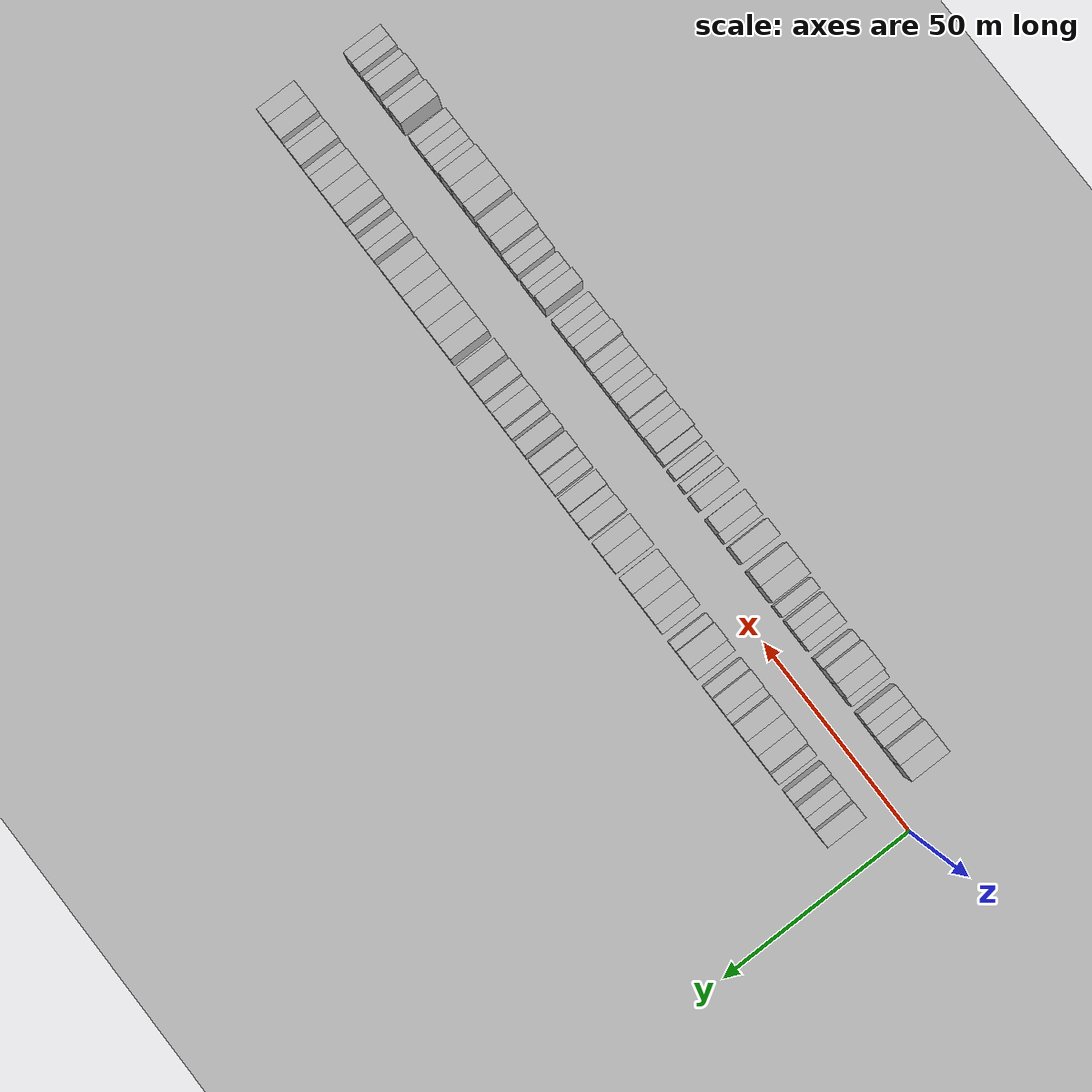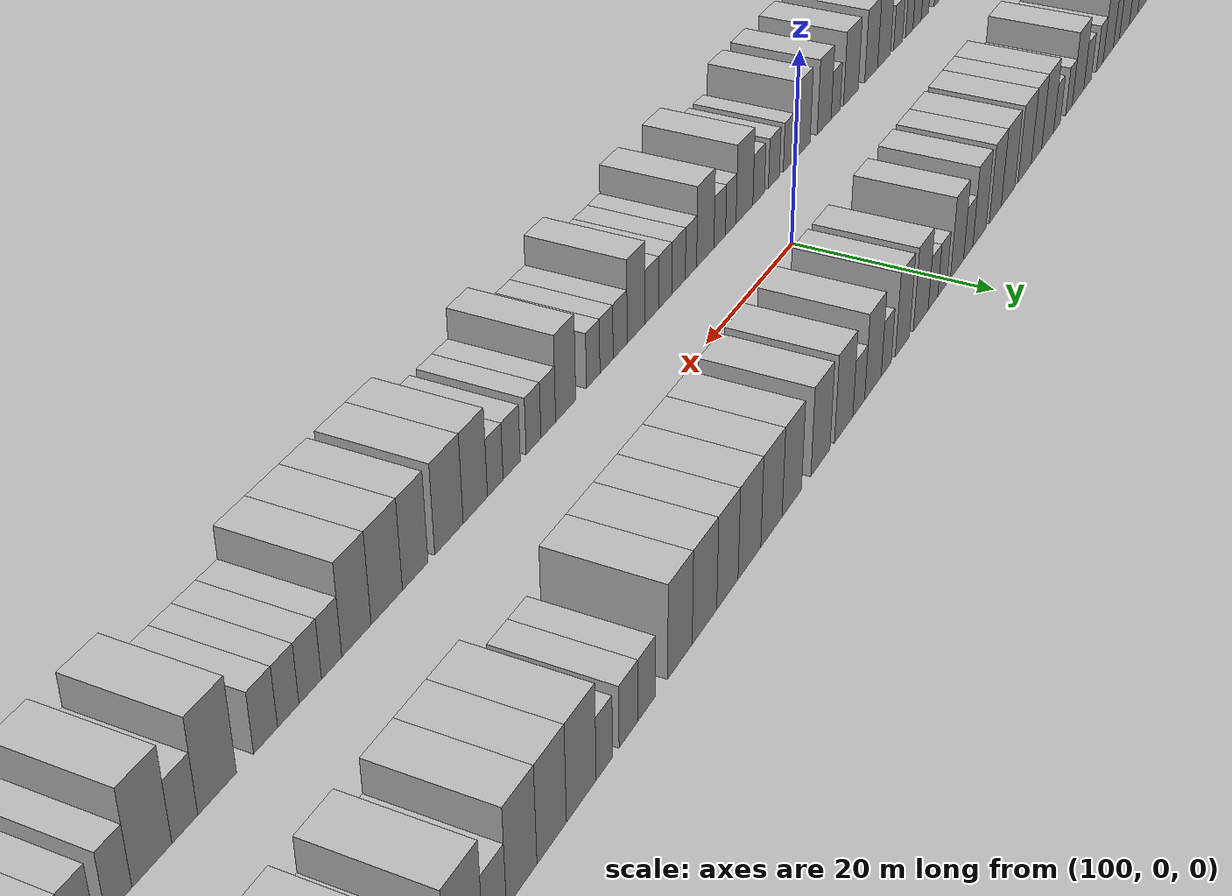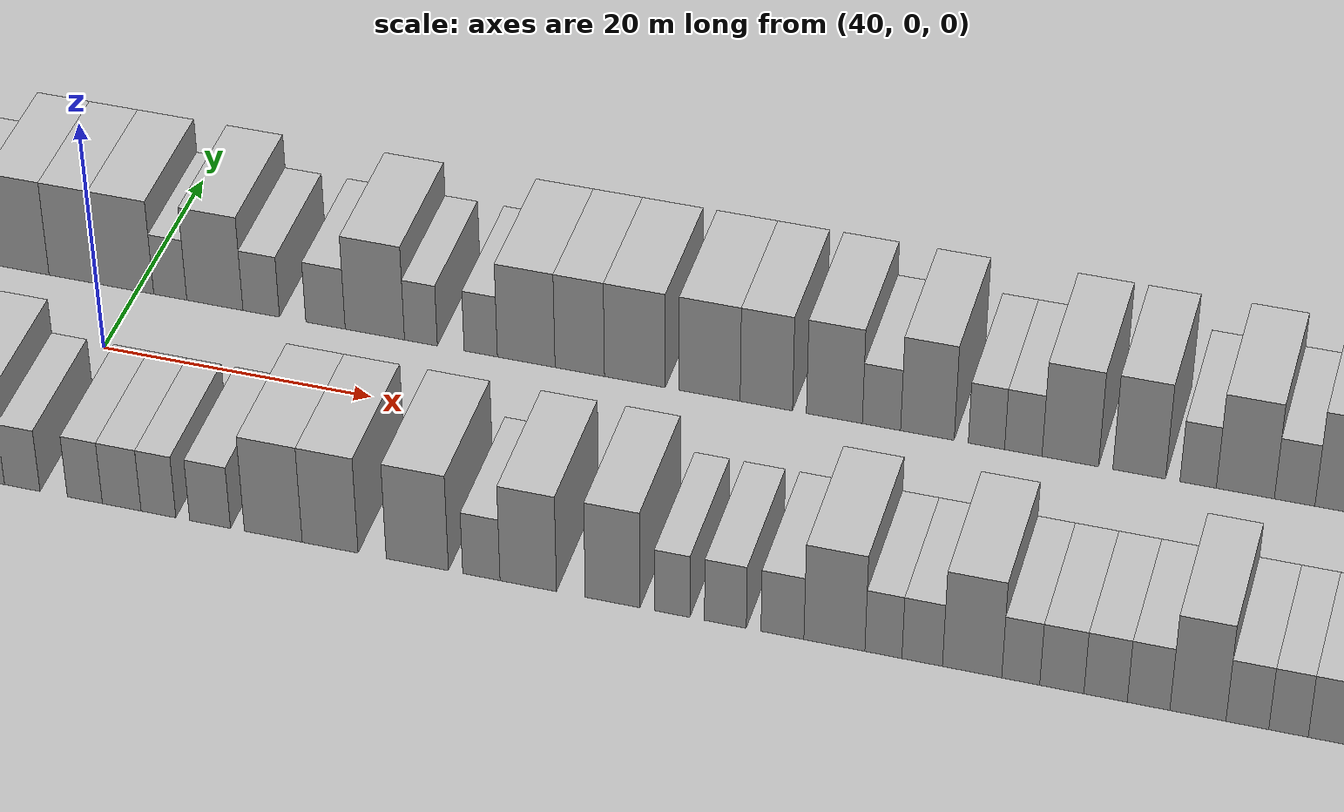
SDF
<?xml version="1.0" encoding="utf-8"?>

<sdf version="1.6">

   <world name="default">

      <gui fullscreen="0">

         <camera name="user_camera">

            <pose>-15 0 4.57585 0 0 0</pose>

            <view_controller>orbit</view_controller>

         </camera>

      </gui>

      <scene>

         <sky>

           <clouds>

             <speed>12</speed>

           </clouds>

         </sky>

         <ambient>0.4 0.4 0.4 1</ambient>

         <background>0.7 0.7 0.7 1</background>

         <shadows>1</shadows>

      </scene>

      <gravity>0 0 -9.8066</gravity>

      <magnetic_field>6e-06 2.3e-05 -4.2e-05</magnetic_field>

      <physics default="0" name="default_physics" type="ode">

         <ode>

            <solver>

               <type>quick</type>

               <iters>10</iters>

               <sor>1.0</sor>

               <use_dynamic_moi_rescaling>0</use_dynamic_moi_rescaling>

            </solver>

            <constraints>

               <cfm>0</cfm>

               <erp>0.2</erp>

               <contact_max_correcting_vel>100</contact_max_correcting_vel>

               <contact_surface_layer>0.001</contact_surface_layer>

            </constraints>

         </ode>

         <max_step_size>0.004</max_step_size>

         <real_time_factor>1</real_time_factor>

         <real_time_update_rate>250</real_time_update_rate>

      </physics>

      <light name="sun" type="directional">

         <cast_shadows>1</cast_shadows>

         <pose>0 0 10 0 0 0</pose>

         <diffuse>0.8 0.8 0.8 1</diffuse>

         <specular>0.2 0.2 0.2 1</specular>

         <attenuation>

            <range>1000</range>

            <constant>0.9</constant>

            <linear>0.01</linear>

            <quadratic>0.001</quadratic>

         </attenuation>

         <direction>-0.5 0.1 -0.9</direction>

      </light>

      <include>

         <name>ground_plane_1</name>

         <uri>model://HANNAS_ground_plane</uri>

         <pose>0 0 0  0 0 0</pose>

      </include>

      <include>

         <name>ground_plane_2</name>

         <uri>model://HANNAS_ground_plane</uri>

         <pose>100 0 0  0 0 0</pose>

      </include>

      <model name="building_1">

         <static>1</static>

         <pose frame="">11.9980 11.0000 0 0.000000 0.000000 1.570796</pose>

         <link name="link">

            <pose frame="">0 0 4.50 0 0 0</pose>

            <collision name="collision">

               <geometry>

                  <box>

                     <size>10.0000 3.9959 9.0000</size>

                  </box>

               </geometry>

               <max_contacts>10</max_contacts>

               <surface>

                  <contact>

                     <ode/>

                  </contact>

                  <bounce/>

                  <friction>

                     <torsional>

                        <ode/>

                     </torsional>

                     <ode/>

                  </friction>

               </surface>

            </collision>

            <visual name="visual">

               <cast_shadows>0</cast_shadows>

               <geometry>

                  <box>

                     <size>10.0000 3.9959 9.0000</size>

                  </box>

               </geometry>

               <material>

                  <script>

                     <uri>model://HANNAS_wall/materials/scripts</uri>

                     <uri>model://HANNAS_wall/materials/textures</uri>

                     <name>vrc/HANNAS_wall</name>

                  </script>

               </material>

            </visual>

            <self_collide>0</self_collide>

            <enable_wind>0</enable_wind>

            <kinematic>0</kinematic>

         </link>

      </model>

      <model name="building_2">

         <static>1</static>

         <pose frame="">15.4072 11.0000 0 0.000000 0.000000 1.570796</pose>

         <link name="link">

            <pose frame="">0 0 3.00 0 0 0</pose>

            <collision name="collision">

               <geometry>

                  <box>

                     <size>10.0000 2.8226 6.0000</size>

                  </box>

               </geometry>

               <max_contacts>10</max_contacts>

               <surface>

                  <contact>

                     <ode/>

                  </contact>

                  <bounce/>

                  <friction>

                     <torsional>

                        <ode/>

                     </torsional>

                     <ode/>

                  </friction>

               </surface>

            </collision>

            <visual name="visual">

               <cast_shadows>0</cast_shadows>

               <geometry>

                  <box>

                     <size>10.0000 2.8226 6.0000</size>

                  </box>

               </geometry>

               <material>

                  <script>

                     <uri>model://HANNAS_wall/materials/scripts</uri>

                     <uri>model://HANNAS_wall/materials/textures</uri>

                     <name>vrc/HANNAS_wall</name>

                  </script>

               </material>

            </visual>

            <self_collide>0</self_collide>

            <enable_wind>0</enable_wind>

            <kinematic>0</kinematic>

         </link>

      </model>

      <model name="building_3">

         <static>1</static>

         <pose frame="">18.2727 11.0000 0 0.000000 0.000000 1.570796</pose>

         <link name="link">

            <pose frame="">0 0 3.00 0 0 0</pose>

            <collision name="collision">

               <geometry>

                  <box>

                     <size>10.0000 2.9083 6.0000</size>

                  </box>

               </geometry>

               <max_contacts>10</max_contacts>

               <surface>

                  <contact>

                     <ode/>

                  </contact>

                  <bounce/>

                  <friction>

                     <torsional>

                        <ode/>

                     </torsional>

                     <ode/>

                  </friction>

               </surface>

            </collision>

            <visual name="visual">

               <cast_shadows>0</cast_shadows>

               <geometry>

                  <box>

                     <size>10.0000 2.9083 6.0000</size>

                  </box>

               </geometry>

               <material>

                  <script>

                     <uri>model://HANNAS_wall/materials/scripts</uri>

                     <uri>model://HANNAS_wall/materials/textures</uri>

                     <name>vrc/HANNAS_wall</name>

                  </script>

               </material>

            </visual>

            <self_collide>0</self_collide>

            <enable_wind>0</enable_wind>

            <kinematic>0</kinematic>

         </link>

      </model>

      <model name="building_4">

         <static>1</static>

         <pose frame="">22.1791 11.0000 0 0.000000 0.000000 1.570796</pose>

         <link name="link">

            <pose frame="">0 0 3.00 0 0 0</pose>

            <collision name="collision">

               <geometry>

                  <box>

                     <size>10.0000 2.9046 6.0000</size>

                  </box>

               </geometry>

               <max_contacts>10</max_contacts>

               <surface>

                  <contact>

                     <ode/>

                  </contact>

                  <bounce/>

                  <friction>

                     <torsional>

                        <ode/>

                     </torsional>

                     <ode/>

                  </friction>

               </surface>

            </collision>

            <visual name="visual">

               <cast_shadows>0</cast_shadows>

               <geometry>

                  <box>

                     <size>10.0000 2.9046 6.0000</size>

                  </box>

               </geometry>

               <material>

                  <script>

                     <uri>model://HANNAS_wall/materials/scripts</uri>

                     <uri>model://HANNAS_wall/materials/textures</uri>

                     <name>vrc/HANNAS_wall</name>

                  </script>

               </material>

            </visual>

            <self_collide>0</self_collide>

            <enable_wind>0</enable_wind>

            <kinematic>0</kinematic>

         </link>

      </model>

      <model name="building_5">

         <static>1</static>

         <pose frame="">26.9787 11.0000 0 0.000000 0.000000 1.570796</pose>

         <link name="link">

            <pose frame="">0 0 3.00 0 0 0</pose>

            <collision name="collision">

               <geometry>

                  <box>

                     <size>10.0000 2.6946 6.0000</size>

                  </box>

               </geometry>

               <max_contacts>10</max_contacts>

               <surface>

                  <contact>

                     <ode/>

                  </contact>

                  <bounce/>

                  <friction>

                     <torsional>

                        <ode/>

                     </torsional>

                     <ode/>

                  </friction>

               </surface>

            </collision>

            <visual name="visual">

               <cast_shadows>0</cast_shadows>

               <geometry>

                  <box>

                     <size>10.0000 2.6946 6.0000</size>

                  </box>

               </geometry>

               <material>

                  <script>

                     <uri>model://HANNAS_wall/materials/scripts</uri>

                     <uri>model://HANNAS_wall/materials/textures</uri>

                     <name>vrc/HANNAS_wall</name>

                  </script>

               </material>

            </visual>

            <self_collide>0</self_collide>

            <enable_wind>0</enable_wind>

            <kinematic>0</kinematic>

         </link>

      </model>

      <model name="building_6">

         <static>1</static>

         <pose frame="">31.3501 11.0000 0 0.000000 0.000000 1.570796</pose>

         <link name="link">

            <pose frame="">0 0 4.50 0 0 0</pose>

            <collision name="collision">

               <geometry>

                  <box>

                     <size>10.0000 4.0482 9.0000</size>

                  </box>

               </geometry>

               <max_contacts>10</max_contacts>

               <surface>

                  <contact>

                     <ode/>

                  </contact>

                  <bounce/>

                  <friction>

                     <torsional>

                        <ode/>

                     </torsional>

                     <ode/>

                  </friction>

               </surface>

            </collision>

            <visual name="visual">

               <cast_shadows>0</cast_shadows>

               <geometry>

                  <box>

                     <size>10.0000 4.0482 9.0000</size>

                  </box>

               </geometry>

               <material>

                  <script>

                     <uri>model://HANNAS_wall/materials/scripts</uri>

                     <uri>model://HANNAS_wall/materials/textures</uri>

                     <name>vrc/HANNAS_wall</name>

                  </script>

               </material>

            </visual>

            <self_collide>0</self_collide>

            <enable_wind>0</enable_wind>

            <kinematic>0</kinematic>

         </link>

      </model>

      <model name="building_7">

         <static>1</static>

         <pose frame="">35.2538 11.0000 0 0.000000 0.000000 1.570796</pose>

         <link name="link">

            <pose frame="">0 0 4.50 0 0 0</pose>

            <collision name="collision">

               <geometry>

                  <box>

                     <size>10.0000 3.7592 9.0000</size>

                  </box>

               </geometry>

               <max_contacts>10</max_contacts>

               <surface>

                  <contact>

                     <ode/>

                  </contact>

                  <bounce/>

                  <friction>

                     <torsional>

                        <ode/>

                     </torsional>

                     <ode/>

                  </friction>

               </surface>

            </collision>

            <visual name="visual">

               <cast_shadows>0</cast_shadows>

               <geometry>

                  <box>

                     <size>10.0000 3.7592 9.0000</size>

                  </box>

               </geometry>

               <material>

                  <script>

                     <uri>model://HANNAS_wall/materials/scripts</uri>

                     <uri>model://HANNAS_wall/materials/textures</uri>

                     <name>vrc/HANNAS_wall</name>

                  </script>

               </material>

            </visual>

            <self_collide>0</self_collide>

            <enable_wind>0</enable_wind>

            <kinematic>0</kinematic>

         </link>

      </model>

      <model name="building_8">

         <static>1</static>

         <pose frame="">39.3070 11.0000 0 0.000000 0.000000 1.570796</pose>

         <link name="link">

            <pose frame="">0 0 4.50 0 0 0</pose>

            <collision name="collision">

               <geometry>

                  <box>

                     <size>10.0000 4.3472 9.0000</size>

                  </box>

               </geometry>

               <max_contacts>10</max_contacts>

               <surface>

                  <contact>

                     <ode/>

                  </contact>

                  <bounce/>

                  <friction>

                     <torsional>

                        <ode/>

                     </torsional>

                     <ode/>

                  </friction>

               </surface>

            </collision>

            <visual name="visual">

               <cast_shadows>0</cast_shadows>

               <geometry>

                  <box>

                     <size>10.0000 4.3472 9.0000</size>

                  </box>

               </geometry>

               <material>

                  <script>

                     <uri>model://HANNAS_wall/materials/scripts</uri>

                     <uri>model://HANNAS_wall/materials/textures</uri>

                     <name>vrc/HANNAS_wall</name>

                  </script>

               </material>

            </visual>

            <self_collide>0</self_collide>

            <enable_wind>0</enable_wind>

            <kinematic>0</kinematic>

         </link>

      </model>

      <model name="building_9">

         <static>1</static>

         <pose frame="">42.7500 11.0000 0 0.000000 0.000000 1.570796</pose>

         <link name="link">

            <pose frame="">0 0 3.00 0 0 0</pose>

            <collision name="collision">

               <geometry>

                  <box>

                     <size>10.0000 2.5387 6.0000</size>

                  </box>

               </geometry>

               <max_contacts>10</max_contacts>

               <surface>

                  <contact>

                     <ode/>

                  </contact>

                  <bounce/>

                  <friction>

                     <torsional>

                        <ode/>

                     </torsional>

                     <ode/>

                  </friction>

               </surface>

            </collision>

            <visual name="visual">

               <cast_shadows>0</cast_shadows>

               <geometry>

                  <box>

                     <size>10.0000 2.5387 6.0000</size>

                  </box>

               </geometry>

               <material>

                  <script>

                     <uri>model://HANNAS_wall/materials/scripts</uri>

                     <uri>model://HANNAS_wall/materials/textures</uri>

                     <name>vrc/HANNAS_wall</name>

                  </script>

               </material>

            </visual>

            <self_collide>0</self_collide>

            <enable_wind>0</enable_wind>

            <kinematic>0</kinematic>

         </link>

      </model>

      <model name="building_10">

         <static>1</static>

         <pose frame="">46.1682 11.0000 0 0.000000 0.000000 1.570796</pose>

         <link name="link">

            <pose frame="">0 0 4.50 0 0 0</pose>

            <collision name="collision">

               <geometry>

                  <box>

                     <size>10.0000 4.2977 9.0000</size>

                  </box>

               </geometry>

               <max_contacts>10</max_contacts>

               <surface>

                  <contact>

                     <ode/>

                  </contact>

                  <bounce/>

                  <friction>

                     <torsional>

                        <ode/>

                     </torsional>

                     <ode/>

                  </friction>

               </surface>

            </collision>

            <visual name="visual">

               <cast_shadows>0</cast_shadows>

               <geometry>

                  <box>

                     <size>10.0000 4.2977 9.0000</size>

                  </box>

               </geometry>

               <material>

                  <script>

                     <uri>model://HANNAS_wall/materials/scripts</uri>

                     <uri>model://HANNAS_wall/materials/textures</uri>

                     <name>vrc/HANNAS_wall</name>

                  </script>

               </material>

            </visual>

            <self_collide>0</self_collide>

            <enable_wind>0</enable_wind>

            <kinematic>0</kinematic>

         </link>

      </model>

      <model name="building_11">

         <static>1</static>

         <pose frame="">49.7075 11.0000 0 0.000000 0.000000 1.570796</pose>

         <link name="link">

            <pose frame="">0 0 3.00 0 0 0</pose>

            <collision name="collision">

               <geometry>

                  <box>

                     <size>10.0000 2.7811 6.0000</size>

                  </box>

               </geometry>

               <max_contacts>10</max_contacts>

               <surface>

                  <contact>

                     <ode/>

                  </contact>

                  <bounce/>

                  <friction>

                     <torsional>

                        <ode/>

                     </torsional>

                     <ode/>

                  </friction>

               </surface>

            </collision>

            <visual name="visual">

               <cast_shadows>0</cast_shadows>

               <geometry>

                  <box>

                     <size>10.0000 2.7811 6.0000</size>

                  </box>

               </geometry>

               <material>

                  <script>

                     <uri>model://HANNAS_wall/materials/scripts</uri>

                     <uri>model://HANNAS_wall/materials/textures</uri>

                     <name>vrc/HANNAS_wall</name>

                  </script>

               </material>

            </visual>

            <self_collide>0</self_collide>

            <enable_wind>0</enable_wind>

            <kinematic>0</kinematic>

         </link>

      </model>

      <model name="building_12">

         <static>1</static>

         <pose frame="">54.5889 11.0000 0 0.000000 0.000000 1.570796</pose>

         <link name="link">

            <pose frame="">0 0 3.00 0 0 0</pose>

            <collision name="collision">

               <geometry>

                  <box>

                     <size>10.0000 2.9816 6.0000</size>

                  </box>

               </geometry>

               <max_contacts>10</max_contacts>

               <surface>

                  <contact>

                     <ode/>

                  </contact>

                  <bounce/>

                  <friction>

                     <torsional>

                        <ode/>

                     </torsional>

                     <ode/>

                  </friction>

               </surface>

            </collision>

            <visual name="visual">

               <cast_shadows>0</cast_shadows>

               <geometry>

                  <box>

                     <size>10.0000 2.9816 6.0000</size>

                  </box>

               </geometry>

               <material>

                  <script>

                     <uri>model://HANNAS_wall/materials/scripts</uri>

                     <uri>model://HANNAS_wall/materials/textures</uri>

                     <name>vrc/HANNAS_wall</name>

                  </script>

               </material>

            </visual>

            <self_collide>0</self_collide>

            <enable_wind>0</enable_wind>

            <kinematic>0</kinematic>

         </link>

      </model>

      <model name="building_13">

         <static>1</static>

         <pose frame="">58.3121 11.0000 0 0.000000 0.000000 1.570796</pose>

         <link name="link">

            <pose frame="">0 0 4.50 0 0 0</pose>

            <collision name="collision">

               <geometry>

                  <box>

                     <size>10.0000 4.4650 9.0000</size>

                  </box>

               </geometry>

               <max_contacts>10</max_contacts>

               <surface>

                  <contact>

                     <ode/>

                  </contact>

                  <bounce/>

                  <friction>

                     <torsional>

                        <ode/>

                     </torsional>

                     <ode/>

                  </friction>

               </surface>

            </collision>

            <visual name="visual">

               <cast_shadows>0</cast_shadows>

               <geometry>

                  <box>

                     <size>10.0000 4.4650 9.0000</size>

                  </box>

               </geometry>

               <material>

                  <script>

                     <uri>model://HANNAS_wall/materials/scripts</uri>

                     <uri>model://HANNAS_wall/materials/textures</uri>

                     <name>vrc/HANNAS_wall</name>

                  </script>

               </material>

            </visual>

            <self_collide>0</self_collide>

            <enable_wind>0</enable_wind>

            <kinematic>0</kinematic>

         </link>

      </model>

      <model name="building_14">

         <static>1</static>

         <pose frame="">61.7764 11.0000 0 0.000000 0.000000 1.570796</pose>

         <link name="link">

            <pose frame="">0 0 3.00 0 0 0</pose>

            <collision name="collision">

               <geometry>

                  <box>

                     <size>10.0000 2.4636 6.0000</size>

                  </box>

               </geometry>

               <max_contacts>10</max_contacts>

               <surface>

                  <contact>

                     <ode/>

                  </contact>

                  <bounce/>

                  <friction>

                     <torsional>

                        <ode/>

                     </torsional>

                     <ode/>

                  </friction>

               </surface>

            </collision>

            <visual name="visual">

               <cast_shadows>0</cast_shadows>

               <geometry>

                  <box>

                     <size>10.0000 2.4636 6.0000</size>

                  </box>

               </geometry>

               <material>

                  <script>

                     <uri>model://HANNAS_wall/materials/scripts</uri>

                     <uri>model://HANNAS_wall/materials/textures</uri>

                     <name>vrc/HANNAS_wall</name>

                  </script>

               </material>

            </visual>

            <self_collide>0</self_collide>

            <enable_wind>0</enable_wind>

            <kinematic>0</kinematic>

         </link>

      </model>

      <model name="building_15">

         <static>1</static>

         <pose frame="">66.2464 11.0000 0 0.000000 0.000000 1.570796</pose>

         <link name="link">

            <pose frame="">0 0 3.00 0 0 0</pose>

            <collision name="collision">

               <geometry>

                  <box>

                     <size>10.0000 2.4763 6.0000</size>

                  </box>

               </geometry>

               <max_contacts>10</max_contacts>

               <surface>

                  <contact>

                     <ode/>

                  </contact>

                  <bounce/>

                  <friction>

                     <torsional>

                        <ode/>

                     </torsional>

                     <ode/>

                  </friction>

               </surface>

            </collision>

            <visual name="visual">

               <cast_shadows>0</cast_shadows>

               <geometry>

                  <box>

                     <size>10.0000 2.4763 6.0000</size>

                  </box>

               </geometry>

               <material>

                  <script>

                     <uri>model://HANNAS_wall/materials/scripts</uri>

                     <uri>model://HANNAS_wall/materials/textures</uri>

                     <name>vrc/HANNAS_wall</name>

                  </script>

               </material>

            </visual>

            <self_collide>0</self_collide>

            <enable_wind>0</enable_wind>

            <kinematic>0</kinematic>

         </link>

      </model>

      <model name="building_16">

         <static>1</static>

         <pose frame="">69.6236 11.0000 0 0.000000 0.000000 1.570796</pose>

         <link name="link">

            <pose frame="">0 0 4.50 0 0 0</pose>

            <collision name="collision">

               <geometry>

                  <box>

                     <size>10.0000 4.2780 9.0000</size>

                  </box>

               </geometry>

               <max_contacts>10</max_contacts>

               <surface>

                  <contact>

                     <ode/>

                  </contact>

                  <bounce/>

                  <friction>

                     <torsional>

                        <ode/>

                     </torsional>

                     <ode/>

                  </friction>

               </surface>

            </collision>

            <visual name="visual">

               <cast_shadows>0</cast_shadows>

               <geometry>

                  <box>

                     <size>10.0000 4.2780 9.0000</size>

                  </box>

               </geometry>

               <material>

                  <script>

                     <uri>model://HANNAS_wall/materials/scripts</uri>

                     <uri>model://HANNAS_wall/materials/textures</uri>

                     <name>vrc/HANNAS_wall</name>

                  </script>

               </material>

            </visual>

            <self_collide>0</self_collide>

            <enable_wind>0</enable_wind>

            <kinematic>0</kinematic>

         </link>

      </model>

      <model name="building_17">

         <static>1</static>

         <pose frame="">73.5857 11.0000 0 0.000000 0.000000 1.570796</pose>

         <link name="link">

            <pose frame="">0 0 4.50 0 0 0</pose>

            <collision name="collision">

               <geometry>

                  <box>

                     <size>10.0000 3.6463 9.0000</size>

                  </box>

               </geometry>

               <max_contacts>10</max_contacts>

               <surface>

                  <contact>

                     <ode/>

                  </contact>

                  <bounce/>

                  <friction>

                     <torsional>

                        <ode/>

                     </torsional>

                     <ode/>

                  </friction>

               </surface>

            </collision>

            <visual name="visual">

               <cast_shadows>0</cast_shadows>

               <geometry>

                  <box>

                     <size>10.0000 3.6463 9.0000</size>

                  </box>

               </geometry>

               <material>

                  <script>

                     <uri>model://HANNAS_wall/materials/scripts</uri>

                     <uri>model://HANNAS_wall/materials/textures</uri>

                     <name>vrc/HANNAS_wall</name>

                  </script>

               </material>

            </visual>

            <self_collide>0</self_collide>

            <enable_wind>0</enable_wind>

            <kinematic>0</kinematic>

         </link>

      </model>

      <model name="building_18">

         <static>1</static>

         <pose frame="">77.6428 11.0000 0 0.000000 0.000000 1.570796</pose>

         <link name="link">

            <pose frame="">0 0 4.50 0 0 0</pose>

            <collision name="collision">

               <geometry>

                  <box>

                     <size>10.0000 4.4679 9.0000</size>

                  </box>

               </geometry>

               <max_contacts>10</max_contacts>

               <surface>

                  <contact>

                     <ode/>

                  </contact>

                  <bounce/>

                  <friction>

                     <torsional>

                        <ode/>

                     </torsional>

                     <ode/>

                  </friction>

               </surface>

            </collision>

            <visual name="visual">

               <cast_shadows>0</cast_shadows>

               <geometry>

                  <box>

                     <size>10.0000 4.4679 9.0000</size>

                  </box>

               </geometry>

               <material>

                  <script>

                     <uri>model://HANNAS_wall/materials/scripts</uri>

                     <uri>model://HANNAS_wall/materials/textures</uri>

                     <name>vrc/HANNAS_wall</name>

                  </script>

               </material>

            </visual>

            <self_collide>0</self_collide>

            <enable_wind>0</enable_wind>

            <kinematic>0</kinematic>

         </link>

      </model>

      <model name="building_19">

         <static>1</static>

         <pose frame="">83.0998 11.0000 0 0.000000 0.000000 1.570796</pose>

         <link name="link">

            <pose frame="">0 0 4.50 0 0 0</pose>

            <collision name="collision">

               <geometry>

                  <box>

                     <size>10.0000 4.4460 9.0000</size>

                  </box>

               </geometry>

               <max_contacts>10</max_contacts>

               <surface>

                  <contact>

                     <ode/>

                  </contact>

                  <bounce/>

                  <friction>

                     <torsional>

                        <ode/>

                     </torsional>

                     <ode/>

                  </friction>

               </surface>

            </collision>

            <visual name="visual">

               <cast_shadows>0</cast_shadows>

               <geometry>

                  <box>

                     <size>10.0000 4.4460 9.0000</size>

                  </box>

               </geometry>

               <material>

                  <script>

                     <uri>model://HANNAS_wall/materials/scripts</uri>

                     <uri>model://HANNAS_wall/materials/textures</uri>

                     <name>vrc/HANNAS_wall</name>

                  </script>

               </material>

            </visual>

            <self_collide>0</self_collide>

            <enable_wind>0</enable_wind>

            <kinematic>0</kinematic>

         </link>

      </model>

      <model name="building_20">

         <static>1</static>

         <pose frame="">87.2193 11.0000 0 0.000000 0.000000 1.570796</pose>

         <link name="link">

            <pose frame="">0 0 4.50 0 0 0</pose>

            <collision name="collision">

               <geometry>

                  <box>

                     <size>10.0000 3.7931 9.0000</size>

                  </box>

               </geometry>

               <max_contacts>10</max_contacts>

               <surface>

                  <contact>

                     <ode/>

                  </contact>

                  <bounce/>

                  <friction>

                     <torsional>

                        <ode/>

                     </torsional>

                     <ode/>

                  </friction>

               </surface>

            </collision>

            <visual name="visual">

               <cast_shadows>0</cast_shadows>

               <geometry>

                  <box>

                     <size>10.0000 3.7931 9.0000</size>

                  </box>

               </geometry>

               <material>

                  <script>

                     <uri>model://HANNAS_wall/materials/scripts</uri>

                     <uri>model://HANNAS_wall/materials/textures</uri>

                     <name>vrc/HANNAS_wall</name>

                  </script>

               </material>

            </visual>

            <self_collide>0</self_collide>

            <enable_wind>0</enable_wind>

            <kinematic>0</kinematic>

         </link>

      </model>

      <model name="building_21">

         <static>1</static>

         <pose frame="">92.1273 11.0000 0 0.000000 0.000000 1.570796</pose>

         <link name="link">

            <pose frame="">0 0 4.50 0 0 0</pose>

            <collision name="collision">

               <geometry>

                  <box>

                     <size>10.0000 4.0228 9.0000</size>

                  </box>

               </geometry>

               <max_contacts>10</max_contacts>

               <surface>

                  <contact>

                     <ode/>

                  </contact>

                  <bounce/>

                  <friction>

                     <torsional>

                        <ode/>

                     </torsional>

                     <ode/>

                  </friction>

               </surface>

            </collision>

            <visual name="visual">

               <cast_shadows>0</cast_shadows>

               <geometry>

                  <box>

                     <size>10.0000 4.0228 9.0000</size>

                  </box>

               </geometry>

               <material>

                  <script>

                     <uri>model://HANNAS_wall/materials/scripts</uri>

                     <uri>model://HANNAS_wall/materials/textures</uri>

                     <name>vrc/HANNAS_wall</name>

                  </script>

               </material>

            </visual>

            <self_collide>0</self_collide>

            <enable_wind>0</enable_wind>

            <kinematic>0</kinematic>

         </link>

      </model>

      <model name="building_22">

         <static>1</static>

         <pose frame="">95.5092 11.0000 0 0.000000 0.000000 1.570796</pose>

         <link name="link">

            <pose frame="">0 0 3.00 0 0 0</pose>

            <collision name="collision">

               <geometry>

                  <box>

                     <size>10.0000 2.7410 6.0000</size>

                  </box>

               </geometry>

               <max_contacts>10</max_contacts>

               <surface>

                  <contact>

                     <ode/>

                  </contact>

                  <bounce/>

                  <friction>

                     <torsional>

                        <ode/>

                     </torsional>

                     <ode/>

                  </friction>

               </surface>

            </collision>

            <visual name="visual">

               <cast_shadows>0</cast_shadows>

               <geometry>

                  <box>

                     <size>10.0000 2.7410 6.0000</size>

                  </box>

               </geometry>

               <material>

                  <script>

                     <uri>model://HANNAS_wall/materials/scripts</uri>

                     <uri>model://HANNAS_wall/materials/textures</uri>

                     <name>vrc/HANNAS_wall</name>

                  </script>

               </material>

            </visual>

            <self_collide>0</self_collide>

            <enable_wind>0</enable_wind>

            <kinematic>0</kinematic>

         </link>

      </model>

      <model name="building_23">

         <static>1</static>

         <pose frame="">98.7910 11.0000 0 0.000000 0.000000 1.570796</pose>

         <link name="link">

            <pose frame="">0 0 4.50 0 0 0</pose>

            <collision name="collision">

               <geometry>

                  <box>

                     <size>10.0000 3.8228 9.0000</size>

                  </box>

               </geometry>

               <max_contacts>10</max_contacts>

               <surface>

                  <contact>

                     <ode/>

                  </contact>

                  <bounce/>

                  <friction>

                     <torsional>

                        <ode/>

                     </torsional>

                     <ode/>

                  </friction>

               </surface>

            </collision>

            <visual name="visual">

               <cast_shadows>0</cast_shadows>

               <geometry>

                  <box>

                     <size>10.0000 3.8228 9.0000</size>

                  </box>

               </geometry>

               <material>

                  <script>

                     <uri>model://HANNAS_wall/materials/scripts</uri>

                     <uri>model://HANNAS_wall/materials/textures</uri>

                     <name>vrc/HANNAS_wall</name>

                  </script>

               </material>

            </visual>

            <self_collide>0</self_collide>

            <enable_wind>0</enable_wind>

            <kinematic>0</kinematic>

         </link>

      </model>

      <model name="building_24">

         <static>1</static>

         <pose frame="">102.9884 11.0000 0 0.000000 0.000000 1.570796</pose>

         <link name="link">

            <pose frame="">0 0 3.00 0 0 0</pose>

            <collision name="collision">

               <geometry>

                  <box>

                     <size>10.0000 2.5720 6.0000</size>

                  </box>

               </geometry>

               <max_contacts>10</max_contacts>

               <surface>

                  <contact>

                     <ode/>

                  </contact>

                  <bounce/>

                  <friction>

                     <torsional>

                        <ode/>

                     </torsional>

                     <ode/>

                  </friction>

               </surface>

            </collision>

            <visual name="visual">

               <cast_shadows>0</cast_shadows>

               <geometry>

                  <box>

                     <size>10.0000 2.5720 6.0000</size>

                  </box>

               </geometry>

               <material>

                  <script>

                     <uri>model://HANNAS_wall/materials/scripts</uri>

                     <uri>model://HANNAS_wall/materials/textures</uri>

                     <name>vrc/HANNAS_wall</name>

                  </script>

               </material>

            </visual>

            <self_collide>0</self_collide>

            <enable_wind>0</enable_wind>

            <kinematic>0</kinematic>

         </link>

      </model>

      <model name="building_25">

         <static>1</static>

         <pose frame="">105.5951 11.0000 0 0.000000 0.000000 1.570796</pose>

         <link name="link">

            <pose frame="">0 0 3.00 0 0 0</pose>

            <collision name="collision">

               <geometry>

                  <box>

                     <size>10.0000 2.6414 6.0000</size>

                  </box>

               </geometry>

               <max_contacts>10</max_contacts>

               <surface>

                  <contact>

                     <ode/>

                  </contact>

                  <bounce/>

                  <friction>

                     <torsional>

                        <ode/>

                     </torsional>

                     <ode/>

                  </friction>

               </surface>

            </collision>

            <visual name="visual">

               <cast_shadows>0</cast_shadows>

               <geometry>

                  <box>

                     <size>10.0000 2.6414 6.0000</size>

                  </box>

               </geometry>

               <material>

                  <script>

                     <uri>model://HANNAS_wall/materials/scripts</uri>

                     <uri>model://HANNAS_wall/materials/textures</uri>

                     <name>vrc/HANNAS_wall</name>

                  </script>

               </material>

            </visual>

            <self_collide>0</self_collide>

            <enable_wind>0</enable_wind>

            <kinematic>0</kinematic>

         </link>

      </model>

      <model name="building_26">

         <static>1</static>

         <pose frame="">108.9048 11.0000 0 0.000000 0.000000 1.570796</pose>

         <link name="link">

            <pose frame="">0 0 4.50 0 0 0</pose>

            <collision name="collision">

               <geometry>

                  <box>

                     <size>10.0000 3.9780 9.0000</size>

                  </box>

               </geometry>

               <max_contacts>10</max_contacts>

               <surface>

                  <contact>

                     <ode/>

                  </contact>

                  <bounce/>

                  <friction>

                     <torsional>

                        <ode/>

                     </torsional>

                     <ode/>

                  </friction>

               </surface>

            </collision>

            <visual name="visual">

               <cast_shadows>0</cast_shadows>

               <geometry>

                  <box>

                     <size>10.0000 3.9780 9.0000</size>

                  </box>

               </geometry>

               <material>

                  <script>

                     <uri>model://HANNAS_wall/materials/scripts</uri>

                     <uri>model://HANNAS_wall/materials/textures</uri>

                     <name>vrc/HANNAS_wall</name>

                  </script>

               </material>

            </visual>

            <self_collide>0</self_collide>

            <enable_wind>0</enable_wind>

            <kinematic>0</kinematic>

         </link>

      </model>

      <model name="building_27">

         <static>1</static>

         <pose frame="">113.7349 11.0000 0 0.000000 0.000000 1.570796</pose>

         <link name="link">

            <pose frame="">0 0 4.50 0 0 0</pose>

            <collision name="collision">

               <geometry>

                  <box>

                     <size>10.0000 3.6821 9.0000</size>

                  </box>

               </geometry>

               <max_contacts>10</max_contacts>

               <surface>

                  <contact>

                     <ode/>

                  </contact>

                  <bounce/>

                  <friction>

                     <torsional>

                        <ode/>

                     </torsional>

                     <ode/>

                  </friction>

               </surface>

            </collision>

            <visual name="visual">

               <cast_shadows>0</cast_shadows>

               <geometry>

                  <box>

                     <size>10.0000 3.6821 9.0000</size>

                  </box>

               </geometry>

               <material>

                  <script>

                     <uri>model://HANNAS_wall/materials/scripts</uri>

                     <uri>model://HANNAS_wall/materials/textures</uri>

                     <name>vrc/HANNAS_wall</name>

                  </script>

               </material>

            </visual>

            <self_collide>0</self_collide>

            <enable_wind>0</enable_wind>

            <kinematic>0</kinematic>

         </link>

      </model>

      <model name="building_28">

         <static>1</static>

         <pose frame="">117.8396 11.0000 0 0.000000 0.000000 1.570796</pose>

         <link name="link">

            <pose frame="">0 0 3.00 0 0 0</pose>

            <collision name="collision">

               <geometry>

                  <box>

                     <size>10.0000 2.5272 6.0000</size>

                  </box>

               </geometry>

               <max_contacts>10</max_contacts>

               <surface>

                  <contact>

                     <ode/>

                  </contact>

                  <bounce/>

                  <friction>

                     <torsional>

                        <ode/>

                     </torsional>

                     <ode/>

                  </friction>

               </surface>

            </collision>

            <visual name="visual">

               <cast_shadows>0</cast_shadows>

               <geometry>

                  <box>

                     <size>10.0000 2.5272 6.0000</size>

                  </box>

               </geometry>

               <material>

                  <script>

                     <uri>model://HANNAS_wall/materials/scripts</uri>

                     <uri>model://HANNAS_wall/materials/textures</uri>

                     <name>vrc/HANNAS_wall</name>

                  </script>

               </material>

            </visual>

            <self_collide>0</self_collide>

            <enable_wind>0</enable_wind>

            <kinematic>0</kinematic>

         </link>

      </model>

      <model name="building_29">

         <static>1</static>

         <pose frame="">121.1098 11.0000 0 0.000000 0.000000 1.570796</pose>

         <link name="link">

            <pose frame="">0 0 4.50 0 0 0</pose>

            <collision name="collision">

               <geometry>

                  <box>

                     <size>10.0000 4.0132 9.0000</size>

                  </box>

               </geometry>

               <max_contacts>10</max_contacts>

               <surface>

                  <contact>

                     <ode/>

                  </contact>

                  <bounce/>

                  <friction>

                     <torsional>

                        <ode/>

                     </torsional>

                     <ode/>

                  </friction>

               </surface>

            </collision>

            <visual name="visual">

               <cast_shadows>0</cast_shadows>

               <geometry>

                  <box>

                     <size>10.0000 4.0132 9.0000</size>

                  </box>

               </geometry>

               <material>

                  <script>

                     <uri>model://HANNAS_wall/materials/scripts</uri>

                     <uri>model://HANNAS_wall/materials/textures</uri>

                     <name>vrc/HANNAS_wall</name>

                  </script>

               </material>

            </visual>

            <self_collide>0</self_collide>

            <enable_wind>0</enable_wind>

            <kinematic>0</kinematic>

         </link>

      </model>

      <model name="building_30">

         <static>1</static>

         <pose frame="">124.5116 11.0000 0 0.000000 0.000000 1.570796</pose>

         <link name="link">

            <pose frame="">0 0 3.00 0 0 0</pose>

            <collision name="collision">

               <geometry>

                  <box>

                     <size>10.0000 2.7904 6.0000</size>

                  </box>

               </geometry>

               <max_contacts>10</max_contacts>

               <surface>

                  <contact>

                     <ode/>

                  </contact>

                  <bounce/>

                  <friction>

                     <torsional>

                        <ode/>

                     </torsional>

                     <ode/>

                  </friction>

               </surface>

            </collision>

            <visual name="visual">

               <cast_shadows>0</cast_shadows>

               <geometry>

                  <box>

                     <size>10.0000 2.7904 6.0000</size>

                  </box>

               </geometry>

               <material>

                  <script>

                     <uri>model://HANNAS_wall/materials/scripts</uri>

                     <uri>model://HANNAS_wall/materials/textures</uri>

                     <name>vrc/HANNAS_wall</name>

                  </script>

               </material>

            </visual>

            <self_collide>0</self_collide>

            <enable_wind>0</enable_wind>

            <kinematic>0</kinematic>

         </link>

      </model>

      <model name="building_31">

         <static>1</static>

         <pose frame="">128.0067 11.0000 0 0.000000 0.000000 1.570796</pose>

         <link name="link">

            <pose frame="">0 0 4.50 0 0 0</pose>

            <collision name="collision">

               <geometry>

                  <box>

                     <size>10.0000 4.1998 9.0000</size>

                  </box>

               </geometry>

               <max_contacts>10</max_contacts>

               <surface>

                  <contact>

                     <ode/>

                  </contact>

                  <bounce/>

                  <friction>

                     <torsional>

                        <ode/>

                     </torsional>

                     <ode/>

                  </friction>

               </surface>

            </collision>

            <visual name="visual">

               <cast_shadows>0</cast_shadows>

               <geometry>

                  <box>

                     <size>10.0000 4.1998 9.0000</size>

                  </box>

               </geometry>

               <material>

                  <script>

                     <uri>model://HANNAS_wall/materials/scripts</uri>

                     <uri>model://HANNAS_wall/materials/textures</uri>

                     <name>vrc/HANNAS_wall</name>

                  </script>

               </material>

            </visual>

            <self_collide>0</self_collide>

            <enable_wind>0</enable_wind>

            <kinematic>0</kinematic>

         </link>

      </model>

      <model name="building_32">

         <static>1</static>

         <pose frame="">133.2052 11.0000 0 0.000000 0.000000 1.570796</pose>

         <link name="link">

            <pose frame="">0 0 4.50 0 0 0</pose>

            <collision name="collision">

               <geometry>

                  <box>

                     <size>10.0000 4.1973 9.0000</size>

                  </box>

               </geometry>

               <max_contacts>10</max_contacts>

               <surface>

                  <contact>

                     <ode/>

                  </contact>

                  <bounce/>

                  <friction>

                     <torsional>

                        <ode/>

                     </torsional>

                     <ode/>

                  </friction>

               </surface>

            </collision>

            <visual name="visual">

               <cast_shadows>0</cast_shadows>

               <geometry>

                  <box>

                     <size>10.0000 4.1973 9.0000</size>

                  </box>

               </geometry>

               <material>

                  <script>

                     <uri>model://HANNAS_wall/materials/scripts</uri>

                     <uri>model://HANNAS_wall/materials/textures</uri>

                     <name>vrc/HANNAS_wall</name>

                  </script>

               </material>

            </visual>

            <self_collide>0</self_collide>

            <enable_wind>0</enable_wind>

            <kinematic>0</kinematic>

         </link>

      </model>

      <model name="building_33">

         <static>1</static>

         <pose frame="">139.3201 11.0000 0 0.000000 0.000000 1.570796</pose>

         <link name="link">

            <pose frame="">0 0 4.50 0 0 0</pose>

            <collision name="collision">

               <geometry>

                  <box>

                     <size>10.0000 4.0323 9.0000</size>

                  </box>

               </geometry>

               <max_contacts>10</max_contacts>

               <surface>

                  <contact>

                     <ode/>

                  </contact>

                  <bounce/>

                  <friction>

                     <torsional>

                        <ode/>

                     </torsional>

                     <ode/>

                  </friction>

               </surface>

            </collision>

            <visual name="visual">

               <cast_shadows>0</cast_shadows>

               <geometry>

                  <box>

                     <size>10.0000 4.0323 9.0000</size>

                  </box>

               </geometry>

               <material>

                  <script>

                     <uri>model://HANNAS_wall/materials/scripts</uri>

                     <uri>model://HANNAS_wall/materials/textures</uri>

                     <name>vrc/HANNAS_wall</name>

                  </script>

               </material>

            </visual>

            <self_collide>0</self_collide>

            <enable_wind>0</enable_wind>

            <kinematic>0</kinematic>

         </link>

      </model>

      <model name="building_34">

         <static>1</static>

         <pose frame="">143.4640 11.0000 0 0.000000 0.000000 1.570796</pose>

         <link name="link">

            <pose frame="">0 0 4.50 0 0 0</pose>

            <collision name="collision">

               <geometry>

                  <box>

                     <size>10.0000 4.2556 9.0000</size>

                  </box>

               </geometry>

               <max_contacts>10</max_contacts>

               <surface>

                  <contact>

                     <ode/>

                  </contact>

                  <bounce/>

                  <friction>

                     <torsional>

                        <ode/>

                     </torsional>

                     <ode/>

                  </friction>

               </surface>

            </collision>

            <visual name="visual">

               <cast_shadows>0</cast_shadows>

               <geometry>

                  <box>

                     <size>10.0000 4.2556 9.0000</size>

                  </box>

               </geometry>

               <material>

                  <script>

                     <uri>model://HANNAS_wall/materials/scripts</uri>

                     <uri>model://HANNAS_wall/materials/textures</uri>

                     <name>vrc/HANNAS_wall</name>

                  </script>

               </material>

            </visual>

            <self_collide>0</self_collide>

            <enable_wind>0</enable_wind>

            <kinematic>0</kinematic>

         </link>

      </model>

      <model name="building_35">

         <static>1</static>

         <pose frame="">147.7761 11.0000 0 0.000000 0.000000 1.570796</pose>

         <link name="link">

            <pose frame="">0 0 4.50 0 0 0</pose>

            <collision name="collision">

               <geometry>

                  <box>

                     <size>10.0000 4.3686 9.0000</size>

                  </box>

               </geometry>

               <max_contacts>10</max_contacts>

               <surface>

                  <contact>

                     <ode/>

                  </contact>

                  <bounce/>

                  <friction>

                     <torsional>

                        <ode/>

                     </torsional>

                     <ode/>

                  </friction>

               </surface>

            </collision>

            <visual name="visual">

               <cast_shadows>0</cast_shadows>

               <geometry>

                  <box>

                     <size>10.0000 4.3686 9.0000</size>

                  </box>

               </geometry>

               <material>

                  <script>

                     <uri>model://HANNAS_wall/materials/scripts</uri>

                     <uri>model://HANNAS_wall/materials/textures</uri>

                     <name>vrc/HANNAS_wall</name>

                  </script>

               </material>

            </visual>

            <self_collide>0</self_collide>

            <enable_wind>0</enable_wind>

            <kinematic>0</kinematic>

         </link>

      </model>

      <model name="building_36">

         <static>1</static>

         <pose frame="">151.9276 11.0000 0 0.000000 0.000000 1.570796</pose>

         <link name="link">

            <pose frame="">0 0 4.50 0 0 0</pose>

            <collision name="collision">

               <geometry>

                  <box>

                     <size>10.0000 3.9345 9.0000</size>

                  </box>

               </geometry>

               <max_contacts>10</max_contacts>

               <surface>

                  <contact>

                     <ode/>

                  </contact>

                  <bounce/>

                  <friction>

                     <torsional>

                        <ode/>

                     </torsional>

                     <ode/>

                  </friction>

               </surface>

            </collision>

            <visual name="visual">

               <cast_shadows>0</cast_shadows>

               <geometry>

                  <box>

                     <size>10.0000 3.9345 9.0000</size>

                  </box>

               </geometry>

               <material>

                  <script>

                     <uri>model://HANNAS_wall/materials/scripts</uri>

                     <uri>model://HANNAS_wall/materials/textures</uri>

                     <name>vrc/HANNAS_wall</name>

                  </script>

               </material>

            </visual>

            <self_collide>0</self_collide>

            <enable_wind>0</enable_wind>

            <kinematic>0</kinematic>

         </link>

      </model>

      <model name="building_37">

         <static>1</static>

         <pose frame="">156.0718 11.0000 0 0.000000 0.000000 1.570796</pose>

         <link name="link">

            <pose frame="">0 0 4.50 0 0 0</pose>

            <collision name="collision">

               <geometry>

                  <box>

                     <size>10.0000 4.3540 9.0000</size>

                  </box>

               </geometry>

               <max_contacts>10</max_contacts>

               <surface>

                  <contact>

                     <ode/>

                  </contact>

                  <bounce/>

                  <friction>

                     <torsional>

                        <ode/>

                     </torsional>

                     <ode/>

                  </friction>

               </surface>

            </collision>

            <visual name="visual">

               <cast_shadows>0</cast_shadows>

               <geometry>

                  <box>

                     <size>10.0000 4.3540 9.0000</size>

                  </box>

               </geometry>

               <material>

                  <script>

                     <uri>model://HANNAS_wall/materials/scripts</uri>

                     <uri>model://HANNAS_wall/materials/textures</uri>

                     <name>vrc/HANNAS_wall</name>

                  </script>

               </material>

            </visual>

            <self_collide>0</self_collide>

            <enable_wind>0</enable_wind>

            <kinematic>0</kinematic>

         </link>

      </model>

      <model name="building_38">

         <static>1</static>

         <pose frame="">160.3389 11.0000 0 0.000000 0.000000 1.570796</pose>

         <link name="link">

            <pose frame="">0 0 4.50 0 0 0</pose>

            <collision name="collision">

               <geometry>

                  <box>

                     <size>10.0000 4.1802 9.0000</size>

                  </box>

               </geometry>

               <max_contacts>10</max_contacts>

               <surface>

                  <contact>

                     <ode/>

                  </contact>

                  <bounce/>

                  <friction>

                     <torsional>

                        <ode/>

                     </torsional>

                     <ode/>

                  </friction>

               </surface>

            </collision>

            <visual name="visual">

               <cast_shadows>0</cast_shadows>

               <geometry>

                  <box>

                     <size>10.0000 4.1802 9.0000</size>

                  </box>

               </geometry>

               <material>

                  <script>

                     <uri>model://HANNAS_wall/materials/scripts</uri>

                     <uri>model://HANNAS_wall/materials/textures</uri>

                     <name>vrc/HANNAS_wall</name>

                  </script>

               </material>

            </visual>

            <self_collide>0</self_collide>

            <enable_wind>0</enable_wind>

            <kinematic>0</kinematic>

         </link>

      </model>

      <model name="building_39">

         <static>1</static>

         <pose frame="">165.8257 11.0000 0 0.000000 0.000000 1.570796</pose>

         <link name="link">

            <pose frame="">0 0 3.00 0 0 0</pose>

            <collision name="collision">

               <geometry>

                  <box>

                     <size>10.0000 2.7934 6.0000</size>

                  </box>

               </geometry>

               <max_contacts>10</max_contacts>

               <surface>

                  <contact>

                     <ode/>

                  </contact>

                  <bounce/>

                  <friction>

                     <torsional>

                        <ode/>

                     </torsional>

                     <ode/>

                  </friction>

               </surface>

            </collision>

            <visual name="visual">

               <cast_shadows>0</cast_shadows>

               <geometry>

                  <box>

                     <size>10.0000 2.7934 6.0000</size>

                  </box>

               </geometry>

               <material>

                  <script>

                     <uri>model://HANNAS_wall/materials/scripts</uri>

                     <uri>model://HANNAS_wall/materials/textures</uri>

                     <name>vrc/HANNAS_wall</name>

                  </script>

               </material>

            </visual>

            <self_collide>0</self_collide>

            <enable_wind>0</enable_wind>

            <kinematic>0</kinematic>

         </link>

      </model>

      <model name="building_40">

         <static>1</static>

         <pose frame="">168.7134 11.0000 0 0.000000 0.000000 1.570796</pose>

         <link name="link">

            <pose frame="">0 0 3.00 0 0 0</pose>

            <collision name="collision">

               <geometry>

                  <box>

                     <size>10.0000 2.9819 6.0000</size>

                  </box>

               </geometry>

               <max_contacts>10</max_contacts>

               <surface>

                  <contact>

                     <ode/>

                  </contact>

                  <bounce/>

                  <friction>

                     <torsional>

                        <ode/>

                     </torsional>

                     <ode/>

                  </friction>

               </surface>

            </collision>

            <visual name="visual">

               <cast_shadows>0</cast_shadows>

               <geometry>

                  <box>

                     <size>10.0000 2.9819 6.0000</size>

                  </box>

               </geometry>

               <material>

                  <script>

                     <uri>model://HANNAS_wall/materials/scripts</uri>

                     <uri>model://HANNAS_wall/materials/textures</uri>

                     <name>vrc/HANNAS_wall</name>

                  </script>

               </material>

            </visual>

            <self_collide>0</self_collide>

            <enable_wind>0</enable_wind>

            <kinematic>0</kinematic>

         </link>

      </model>

      <model name="building_41">

         <static>1</static>

         <pose frame="">172.4298 11.0000 0 0.000000 0.000000 1.570796</pose>

         <link name="link">

            <pose frame="">0 0 3.00 0 0 0</pose>

            <collision name="collision">

               <geometry>

                  <box>

                     <size>10.0000 2.4508 6.0000</size>

                  </box>

               </geometry>

               <max_contacts>10</max_contacts>

               <surface>

                  <contact>

                     <ode/>

                  </contact>

                  <bounce/>

                  <friction>

                     <torsional>

                        <ode/>

                     </torsional>

                     <ode/>

                  </friction>

               </surface>

            </collision>

            <visual name="visual">

               <cast_shadows>0</cast_shadows>

               <geometry>

                  <box>

                     <size>10.0000 2.4508 6.0000</size>

                  </box>

               </geometry>

               <material>

                  <script>

                     <uri>model://HANNAS_wall/materials/scripts</uri>

                     <uri>model://HANNAS_wall/materials/textures</uri>

                     <name>vrc/HANNAS_wall</name>

                  </script>

               </material>

            </visual>

            <self_collide>0</self_collide>

            <enable_wind>0</enable_wind>

            <kinematic>0</kinematic>

         </link>

      </model>

      <model name="building_42">

         <static>1</static>

         <pose frame="">175.8117 11.0000 0 0.000000 0.000000 1.570796</pose>

         <link name="link">

            <pose frame="">0 0 4.50 0 0 0</pose>

            <collision name="collision">

               <geometry>

                  <box>

                     <size>10.0000 4.3130 9.0000</size>

                  </box>

               </geometry>

               <max_contacts>10</max_contacts>

               <surface>

                  <contact>

                     <ode/>

                  </contact>

                  <bounce/>

                  <friction>

                     <torsional>

                        <ode/>

                     </torsional>

                     <ode/>

                  </friction>

               </surface>

            </collision>

            <visual name="visual">

               <cast_shadows>0</cast_shadows>

               <geometry>

                  <box>

                     <size>10.0000 4.3130 9.0000</size>

                  </box>

               </geometry>

               <material>

                  <script>

                     <uri>model://HANNAS_wall/materials/scripts</uri>

                     <uri>model://HANNAS_wall/materials/textures</uri>

                     <name>vrc/HANNAS_wall</name>

                  </script>

               </material>

            </visual>

            <self_collide>0</self_collide>

            <enable_wind>0</enable_wind>

            <kinematic>0</kinematic>

         </link>

      </model>

      <model name="building_43">

         <static>1</static>

         <pose frame="">180.0138 11.0000 0 0.000000 0.000000 1.570796</pose>

         <link name="link">

            <pose frame="">0 0 4.50 0 0 0</pose>

            <collision name="collision">

               <geometry>

                  <box>

                     <size>10.0000 4.0911 9.0000</size>

                  </box>

               </geometry>

               <max_contacts>10</max_contacts>

               <surface>

                  <contact>

                     <ode/>

                  </contact>

                  <bounce/>

                  <friction>

                     <torsional>

                        <ode/>

                     </torsional>

                     <ode/>

                  </friction>

               </surface>

            </collision>

            <visual name="visual">

               <cast_shadows>0</cast_shadows>

               <geometry>

                  <box>

                     <size>10.0000 4.0911 9.0000</size>

                  </box>

               </geometry>

               <material>

                  <script>

                     <uri>model://HANNAS_wall/materials/scripts</uri>

                     <uri>model://HANNAS_wall/materials/textures</uri>

                     <name>vrc/HANNAS_wall</name>

                  </script>

               </material>

            </visual>

            <self_collide>0</self_collide>

            <enable_wind>0</enable_wind>

            <kinematic>0</kinematic>

         </link>

      </model>

      <model name="building_44">

         <static>1</static>

         <pose frame="">184.0826 11.0000 0 0.000000 0.000000 1.570796</pose>

         <link name="link">

            <pose frame="">0 0 4.50 0 0 0</pose>

            <collision name="collision">

               <geometry>

                  <box>

                     <size>10.0000 4.0466 9.0000</size>

                  </box>

               </geometry>

               <max_contacts>10</max_contacts>

               <surface>

                  <contact>

                     <ode/>

                  </contact>

                  <bounce/>

                  <friction>

                     <torsional>

                        <ode/>

                     </torsional>

                     <ode/>

                  </friction>

               </surface>

            </collision>

            <visual name="visual">

               <cast_shadows>0</cast_shadows>

               <geometry>

                  <box>

                     <size>10.0000 4.0466 9.0000</size>

                  </box>

               </geometry>

               <material>

                  <script>

                     <uri>model://HANNAS_wall/materials/scripts</uri>

                     <uri>model://HANNAS_wall/materials/textures</uri>

                     <name>vrc/HANNAS_wall</name>

                  </script>

               </material>

            </visual>

            <self_collide>0</self_collide>

            <enable_wind>0</enable_wind>

            <kinematic>0</kinematic>

         </link>

      </model>

      <model name="building_45">

         <static>1</static>

         <pose frame="">187.5892 11.0000 0 0.000000 0.000000 1.570796</pose>

         <link name="link">

            <pose frame="">0 0 3.00 0 0 0</pose>

            <collision name="collision">

               <geometry>

                  <box>

                     <size>10.0000 2.9666 6.0000</size>

                  </box>

               </geometry>

               <max_contacts>10</max_contacts>

               <surface>

                  <contact>

                     <ode/>

                  </contact>

                  <bounce/>

                  <friction>

                     <torsional>

                        <ode/>

                     </torsional>

                     <ode/>

                  </friction>

               </surface>

            </collision>

            <visual name="visual">

               <cast_shadows>0</cast_shadows>

               <geometry>

                  <box>

                     <size>10.0000 2.9666 6.0000</size>

                  </box>

               </geometry>

               <material>

                  <script>

                     <uri>model://HANNAS_wall/materials/scripts</uri>

                     <uri>model://HANNAS_wall/materials/textures</uri>

                     <name>vrc/HANNAS_wall</name>

                  </script>

               </material>

            </visual>

            <self_collide>0</self_collide>

            <enable_wind>0</enable_wind>

            <kinematic>0</kinematic>

         </link>

      </model>

      <model name="building_46">

         <static>1</static>

         <pose frame="">191.2856 11.0000 0 0.000000 0.000000 1.570796</pose>

         <link name="link">

            <pose frame="">0 0 4.50 0 0 0</pose>

            <collision name="collision">

               <geometry>

                  <box>

                     <size>10.0000 4.4262 9.0000</size>

                  </box>

               </geometry>

               <max_contacts>10</max_contacts>

               <surface>

                  <contact>

                     <ode/>

                  </contact>

                  <bounce/>

                  <friction>

                     <torsional>

                        <ode/>

                     </torsional>

                     <ode/>

                  </friction>

               </surface>

            </collision>

            <visual name="visual">

               <cast_shadows>0</cast_shadows>

               <geometry>

                  <box>

                     <size>10.0000 4.4262 9.0000</size>

                  </box>

               </geometry>

               <material>

                  <script>

                     <uri>model://HANNAS_wall/materials/scripts</uri>

                     <uri>model://HANNAS_wall/materials/textures</uri>

                     <name>vrc/HANNAS_wall</name>

                  </script>

               </material>

            </visual>

            <self_collide>0</self_collide>

            <enable_wind>0</enable_wind>

            <kinematic>0</kinematic>

         </link>

      </model>

      <model name="building_47">

         <static>1</static>

         <pose frame="">194.7853 11.0000 0 0.000000 0.000000 1.570796</pose>

         <link name="link">

            <pose frame="">0 0 3.00 0 0 0</pose>

            <collision name="collision">

               <geometry>

                  <box>

                     <size>10.0000 2.5732 6.0000</size>

                  </box>

               </geometry>

               <max_contacts>10</max_contacts>

               <surface>

                  <contact>

                     <ode/>

                  </contact>

                  <bounce/>

                  <friction>

                     <torsional>

                        <ode/>

                     </torsional>

                     <ode/>

                  </friction>

               </surface>

            </collision>

            <visual name="visual">

               <cast_shadows>0</cast_shadows>

               <geometry>

                  <box>

                     <size>10.0000 2.5732 6.0000</size>

                  </box>

               </geometry>

               <material>

                  <script>

                     <uri>model://HANNAS_wall/materials/scripts</uri>

                     <uri>model://HANNAS_wall/materials/textures</uri>

                     <name>vrc/HANNAS_wall</name>

                  </script>

               </material>

            </visual>

            <self_collide>0</self_collide>

            <enable_wind>0</enable_wind>

            <kinematic>0</kinematic>

         </link>

      </model>

      <model name="building_48">

         <static>1</static>

         <pose frame="">198.2631 11.0000 0 0.000000 0.000000 1.570796</pose>

         <link name="link">

            <pose frame="">0 0 4.50 0 0 0</pose>

            <collision name="collision">

               <geometry>

                  <box>

                     <size>10.0000 4.3825 9.0000</size>

                  </box>

               </geometry>

               <max_contacts>10</max_contacts>

               <surface>

                  <contact>

                     <ode/>

                  </contact>

                  <bounce/>

                  <friction>

                     <torsional>

                        <ode/>

                     </torsional>

                     <ode/>

                  </friction>

               </surface>

            </collision>

            <visual name="visual">

               <cast_shadows>0</cast_shadows>

               <geometry>

                  <box>

                     <size>10.0000 4.3825 9.0000</size>

                  </box>

               </geometry>

               <material>

                  <script>

                     <uri>model://HANNAS_wall/materials/scripts</uri>

                     <uri>model://HANNAS_wall/materials/textures</uri>

                     <name>vrc/HANNAS_wall</name>

                  </script>

               </material>

            </visual>

            <self_collide>0</self_collide>

            <enable_wind>0</enable_wind>

            <kinematic>0</kinematic>

         </link>

      </model>

      <model name="building_49">

         <static>1</static>

         <pose frame="">202.4168 11.0000 0 0.000000 0.000000 1.570796</pose>

         <link name="link">

            <pose frame="">0 0 4.50 0 0 0</pose>

            <collision name="collision">

               <geometry>

                  <box>

                     <size>10.0000 3.9248 9.0000</size>

                  </box>

               </geometry>

               <max_contacts>10</max_contacts>

               <surface>

                  <contact>

                     <ode/>

                  </contact>

                  <bounce/>

                  <friction>

                     <torsional>

                        <ode/>

                     </torsional>

                     <ode/>

                  </friction>

               </surface>

            </collision>

            <visual name="visual">

               <cast_shadows>0</cast_shadows>

               <geometry>

                  <box>

                     <size>10.0000 3.9248 9.0000</size>

                  </box>

               </geometry>

               <material>

                  <script>

                     <uri>model://HANNAS_wall/materials/scripts</uri>

                     <uri>model://HANNAS_wall/materials/textures</uri>

                     <name>vrc/HANNAS_wall</name>

                  </script>

               </material>

            </visual>

            <self_collide>0</self_collide>

            <enable_wind>0</enable_wind>

            <kinematic>0</kinematic>

         </link>

      </model>

      <model name="building_50">

         <static>1</static>

         <pose frame="">12.0243 -11.0000 0 0.000000 0.000000 1.570796</pose>

         <link name="link">

            <pose frame="">0 0 4.50 0 0 0</pose>

            <collision name="collision">

               <geometry>

                  <box>

                     <size>10.0000 4.0487 9.0000</size>

                  </box>

               </geometry>

               <max_contacts>10</max_contacts>

               <surface>

                  <contact>

                     <ode/>

                  </contact>

                  <bounce/>

                  <friction>

                     <torsional>

                        <ode/>

                     </torsional>

                     <ode/>

                  </friction>

               </surface>

            </collision>

            <visual name="visual">

               <cast_shadows>0</cast_shadows>

               <geometry>

                  <box>

                     <size>10.0000 4.0487 9.0000</size>

                  </box>

               </geometry>

               <material>

                  <script>

                     <uri>model://HANNAS_wall/materials/scripts</uri>

                     <uri>model://HANNAS_wall/materials/textures</uri>

                     <name>vrc/HANNAS_wall</name>

                  </script>

               </material>

            </visual>

            <self_collide>0</self_collide>

            <enable_wind>0</enable_wind>

            <kinematic>0</kinematic>

         </link>

      </model>

      <model name="building_51">

         <static>1</static>

         <pose frame="">16.1841 -11.0000 0 0.000000 0.000000 1.570796</pose>

         <link name="link">

            <pose frame="">0 0 4.50 0 0 0</pose>

            <collision name="collision">

               <geometry>

                  <box>

                     <size>10.0000 4.2708 9.0000</size>

                  </box>

               </geometry>

               <max_contacts>10</max_contacts>

               <surface>

                  <contact>

                     <ode/>

                  </contact>

                  <bounce/>

                  <friction>

                     <torsional>

                        <ode/>

                     </torsional>

                     <ode/>

                  </friction>

               </surface>

            </collision>

            <visual name="visual">

               <cast_shadows>0</cast_shadows>

               <geometry>

                  <box>

                     <size>10.0000 4.2708 9.0000</size>

                  </box>

               </geometry>

               <material>

                  <script>

                     <uri>model://HANNAS_wall/materials/scripts</uri>

                     <uri>model://HANNAS_wall/materials/textures</uri>

                     <name>vrc/HANNAS_wall</name>

                  </script>

               </material>

            </visual>

            <self_collide>0</self_collide>

            <enable_wind>0</enable_wind>

            <kinematic>0</kinematic>

         </link>

      </model>

      <model name="building_52">

         <static>1</static>

         <pose frame="">19.7863 -11.0000 0 0.000000 0.000000 1.570796</pose>

         <link name="link">

            <pose frame="">0 0 3.00 0 0 0</pose>

            <collision name="collision">

               <geometry>

                  <box>

                     <size>10.0000 2.9337 6.0000</size>

                  </box>

               </geometry>

               <max_contacts>10</max_contacts>

               <surface>

                  <contact>

                     <ode/>

                  </contact>

                  <bounce/>

                  <friction>

                     <torsional>

                        <ode/>

                     </torsional>

                     <ode/>

                  </friction>

               </surface>

            </collision>

            <visual name="visual">

               <cast_shadows>0</cast_shadows>

               <geometry>

                  <box>

                     <size>10.0000 2.9337 6.0000</size>

                  </box>

               </geometry>

               <material>

                  <script>

                     <uri>model://HANNAS_wall/materials/scripts</uri>

                     <uri>model://HANNAS_wall/materials/textures</uri>

                     <name>vrc/HANNAS_wall</name>

                  </script>

               </material>

            </visual>

            <self_collide>0</self_collide>

            <enable_wind>0</enable_wind>

            <kinematic>0</kinematic>

         </link>

      </model>

      <model name="building_53">

         <static>1</static>

         <pose frame="">22.7130 -11.0000 0 0.000000 0.000000 1.570796</pose>

         <link name="link">

            <pose frame="">0 0 3.00 0 0 0</pose>

            <collision name="collision">

               <geometry>

                  <box>

                     <size>10.0000 2.9197 6.0000</size>

                  </box>

               </geometry>

               <max_contacts>10</max_contacts>

               <surface>

                  <contact>

                     <ode/>

                  </contact>

                  <bounce/>

                  <friction>

                     <torsional>

                        <ode/>

                     </torsional>

                     <ode/>

                  </friction>

               </surface>

            </collision>

            <visual name="visual">

               <cast_shadows>0</cast_shadows>

               <geometry>

                  <box>

                     <size>10.0000 2.9197 6.0000</size>

                  </box>

               </geometry>

               <material>

                  <script>

                     <uri>model://HANNAS_wall/materials/scripts</uri>

                     <uri>model://HANNAS_wall/materials/textures</uri>

                     <name>vrc/HANNAS_wall</name>

                  </script>

               </material>

            </visual>

            <self_collide>0</self_collide>

            <enable_wind>0</enable_wind>

            <kinematic>0</kinematic>

         </link>

      </model>

      <model name="building_54">

         <static>1</static>

         <pose frame="">25.6211 -11.0000 0 0.000000 0.000000 1.570796</pose>

         <link name="link">

            <pose frame="">0 0 3.00 0 0 0</pose>

            <collision name="collision">

               <geometry>

                  <box>

                     <size>10.0000 2.8964 6.0000</size>

                  </box>

               </geometry>

               <max_contacts>10</max_contacts>

               <surface>

                  <contact>

                     <ode/>

                  </contact>

                  <bounce/>

                  <friction>

                     <torsional>

                        <ode/>

                     </torsional>

                     <ode/>

                  </friction>

               </surface>

            </collision>

            <visual name="visual">

               <cast_shadows>0</cast_shadows>

               <geometry>

                  <box>

                     <size>10.0000 2.8964 6.0000</size>

                  </box>

               </geometry>

               <material>

                  <script>

                     <uri>model://HANNAS_wall/materials/scripts</uri>

                     <uri>model://HANNAS_wall/materials/textures</uri>

                     <name>vrc/HANNAS_wall</name>

                  </script>

               </material>

            </visual>

            <self_collide>0</self_collide>

            <enable_wind>0</enable_wind>

            <kinematic>0</kinematic>

         </link>

      </model>

      <model name="building_55">

         <static>1</static>

         <pose frame="">30.2984 -11.0000 0 0.000000 0.000000 1.570796</pose>

         <link name="link">

            <pose frame="">0 0 3.00 0 0 0</pose>

            <collision name="collision">

               <geometry>

                  <box>

                     <size>10.0000 2.4581 6.0000</size>

                  </box>

               </geometry>

               <max_contacts>10</max_contacts>

               <surface>

                  <contact>

                     <ode/>

                  </contact>

                  <bounce/>

                  <friction>

                     <torsional>

                        <ode/>

                     </torsional>

                     <ode/>

                  </friction>

               </surface>

            </collision>

            <visual name="visual">

               <cast_shadows>0</cast_shadows>

               <geometry>

                  <box>

                     <size>10.0000 2.4581 6.0000</size>

                  </box>

               </geometry>

               <material>

                  <script>

                     <uri>model://HANNAS_wall/materials/scripts</uri>

                     <uri>model://HANNAS_wall/materials/textures</uri>

                     <name>vrc/HANNAS_wall</name>

                  </script>

               </material>

            </visual>

            <self_collide>0</self_collide>

            <enable_wind>0</enable_wind>

            <kinematic>0</kinematic>

         </link>

      </model>

      <model name="building_56">

         <static>1</static>

         <pose frame="">33.3546 -11.0000 0 0.000000 0.000000 1.570796</pose>

         <link name="link">

            <pose frame="">0 0 4.50 0 0 0</pose>

            <collision name="collision">

               <geometry>

                  <box>

                     <size>10.0000 3.6543 9.0000</size>

                  </box>

               </geometry>

               <max_contacts>10</max_contacts>

               <surface>

                  <contact>

                     <ode/>

                  </contact>

                  <bounce/>

                  <friction>

                     <torsional>

                        <ode/>

                     </torsional>

                     <ode/>

                  </friction>

               </surface>

            </collision>

            <visual name="visual">

               <cast_shadows>0</cast_shadows>

               <geometry>

                  <box>

                     <size>10.0000 3.6543 9.0000</size>

                  </box>

               </geometry>

               <material>

                  <script>

                     <uri>model://HANNAS_wall/materials/scripts</uri>

                     <uri>model://HANNAS_wall/materials/textures</uri>

                     <name>vrc/HANNAS_wall</name>

                  </script>

               </material>

            </visual>

            <self_collide>0</self_collide>

            <enable_wind>0</enable_wind>

            <kinematic>0</kinematic>

         </link>

      </model>

      <model name="building_57">

         <static>1</static>

         <pose frame="">37.0646 -11.0000 0 0.000000 0.000000 1.570796</pose>

         <link name="link">

            <pose frame="">0 0 4.50 0 0 0</pose>

            <collision name="collision">

               <geometry>

                  <box>

                     <size>10.0000 3.7656 9.0000</size>

                  </box>

               </geometry>

               <max_contacts>10</max_contacts>

               <surface>

                  <contact>

                     <ode/>

                  </contact>

                  <bounce/>

                  <friction>

                     <torsional>

                        <ode/>

                     </torsional>

                     <ode/>

                  </friction>

               </surface>

            </collision>

            <visual name="visual">

               <cast_shadows>0</cast_shadows>

               <geometry>

                  <box>

                     <size>10.0000 3.7656 9.0000</size>

                  </box>

               </geometry>

               <material>

                  <script>

                     <uri>model://HANNAS_wall/materials/scripts</uri>

                     <uri>model://HANNAS_wall/materials/textures</uri>

                     <name>vrc/HANNAS_wall</name>

                  </script>

               </material>

            </visual>

            <self_collide>0</self_collide>

            <enable_wind>0</enable_wind>

            <kinematic>0</kinematic>

         </link>

      </model>

      <model name="building_58">

         <static>1</static>

         <pose frame="">40.2543 -11.0000 0 0.000000 0.000000 1.570796</pose>

         <link name="link">

            <pose frame="">0 0 3.00 0 0 0</pose>

            <collision name="collision">

               <geometry>

                  <box>

                     <size>10.0000 2.6139 6.0000</size>

                  </box>

               </geometry>

               <max_contacts>10</max_contacts>

               <surface>

                  <contact>

                     <ode/>

                  </contact>

                  <bounce/>

                  <friction>

                     <torsional>

                        <ode/>

                     </torsional>

                     <ode/>

                  </friction>

               </surface>

            </collision>

            <visual name="visual">

               <cast_shadows>0</cast_shadows>

               <geometry>

                  <box>

                     <size>10.0000 2.6139 6.0000</size>

                  </box>

               </geometry>

               <material>

                  <script>

                     <uri>model://HANNAS_wall/materials/scripts</uri>

                     <uri>model://HANNAS_wall/materials/textures</uri>

                     <name>vrc/HANNAS_wall</name>

                  </script>

               </material>

            </visual>

            <self_collide>0</self_collide>

            <enable_wind>0</enable_wind>

            <kinematic>0</kinematic>

         </link>

      </model>

      <model name="building_59">

         <static>1</static>

         <pose frame="">44.8411 -11.0000 0 0.000000 0.000000 1.570796</pose>

         <link name="link">

            <pose frame="">0 0 3.00 0 0 0</pose>

            <collision name="collision">

               <geometry>

                  <box>

                     <size>10.0000 2.5596 6.0000</size>

                  </box>

               </geometry>

               <max_contacts>10</max_contacts>

               <surface>

                  <contact>

                     <ode/>

                  </contact>

                  <bounce/>

                  <friction>

                     <torsional>

                        <ode/>

                     </torsional>

                     <ode/>

                  </friction>

               </surface>

            </collision>

            <visual name="visual">

               <cast_shadows>0</cast_shadows>

               <geometry>

                  <box>

                     <size>10.0000 2.5596 6.0000</size>

                  </box>

               </geometry>

               <material>

                  <script>

                     <uri>model://HANNAS_wall/materials/scripts</uri>

                     <uri>model://HANNAS_wall/materials/textures</uri>

                     <name>vrc/HANNAS_wall</name>

                  </script>

               </material>

            </visual>

            <self_collide>0</self_collide>

            <enable_wind>0</enable_wind>

            <kinematic>0</kinematic>

         </link>

      </model>

      <model name="building_60">

         <static>1</static>

         <pose frame="">47.5301 -11.0000 0 0.000000 0.000000 1.570796</pose>

         <link name="link">

            <pose frame="">0 0 3.00 0 0 0</pose>

            <collision name="collision">

               <geometry>

                  <box>

                     <size>10.0000 2.8185 6.0000</size>

                  </box>

               </geometry>

               <max_contacts>10</max_contacts>

               <surface>

                  <contact>

                     <ode/>

                  </contact>

                  <bounce/>

                  <friction>

                     <torsional>

                        <ode/>

                     </torsional>

                     <ode/>

                  </friction>

               </surface>

            </collision>

            <visual name="visual">

               <cast_shadows>0</cast_shadows>

               <geometry>

                  <box>

                     <size>10.0000 2.8185 6.0000</size>

                  </box>

               </geometry>

               <material>

                  <script>

                     <uri>model://HANNAS_wall/materials/scripts</uri>

                     <uri>model://HANNAS_wall/materials/textures</uri>

                     <name>vrc/HANNAS_wall</name>

                  </script>

               </material>

            </visual>

            <self_collide>0</self_collide>

            <enable_wind>0</enable_wind>

            <kinematic>0</kinematic>

         </link>

      </model>

      <model name="building_61">

         <static>1</static>

         <pose frame="">50.2014 -11.0000 0 0.000000 0.000000 1.570796</pose>

         <link name="link">

            <pose frame="">0 0 3.00 0 0 0</pose>

            <collision name="collision">

               <geometry>

                  <box>

                     <size>10.0000 2.5240 6.0000</size>

                  </box>

               </geometry>

               <max_contacts>10</max_contacts>

               <surface>

                  <contact>

                     <ode/>

                  </contact>

                  <bounce/>

                  <friction>

                     <torsional>

                        <ode/>

                     </torsional>

                     <ode/>

                  </friction>

               </surface>

            </collision>

            <visual name="visual">

               <cast_shadows>0</cast_shadows>

               <geometry>

                  <box>

                     <size>10.0000 2.5240 6.0000</size>

                  </box>

               </geometry>

               <material>

                  <script>

                     <uri>model://HANNAS_wall/materials/scripts</uri>

                     <uri>model://HANNAS_wall/materials/textures</uri>

                     <name>vrc/HANNAS_wall</name>

                  </script>

               </material>

            </visual>

            <self_collide>0</self_collide>

            <enable_wind>0</enable_wind>

            <kinematic>0</kinematic>

         </link>

      </model>

      <model name="building_62">

         <static>1</static>

         <pose frame="">53.9348 -11.0000 0 0.000000 0.000000 1.570796</pose>

         <link name="link">

            <pose frame="">0 0 3.00 0 0 0</pose>

            <collision name="collision">

               <geometry>

                  <box>

                     <size>10.0000 2.9428 6.0000</size>

                  </box>

               </geometry>

               <max_contacts>10</max_contacts>

               <surface>

                  <contact>

                     <ode/>

                  </contact>

                  <bounce/>

                  <friction>

                     <torsional>

                        <ode/>

                     </torsional>

                     <ode/>

                  </friction>

               </surface>

            </collision>

            <visual name="visual">

               <cast_shadows>0</cast_shadows>

               <geometry>

                  <box>

                     <size>10.0000 2.9428 6.0000</size>

                  </box>

               </geometry>

               <material>

                  <script>

                     <uri>model://HANNAS_wall/materials/scripts</uri>

                     <uri>model://HANNAS_wall/materials/textures</uri>

                     <name>vrc/HANNAS_wall</name>

                  </script>

               </material>

            </visual>

            <self_collide>0</self_collide>

            <enable_wind>0</enable_wind>

            <kinematic>0</kinematic>

         </link>

      </model>

      <model name="building_63">

         <static>1</static>

         <pose frame="">58.4784 -11.0000 0 0.000000 0.000000 1.570796</pose>

         <link name="link">

            <pose frame="">0 0 4.50 0 0 0</pose>

            <collision name="collision">

               <geometry>

                  <box>

                     <size>10.0000 4.1446 9.0000</size>

                  </box>

               </geometry>

               <max_contacts>10</max_contacts>

               <surface>

                  <contact>

                     <ode/>

                  </contact>

                  <bounce/>

                  <friction>

                     <torsional>

                        <ode/>

                     </torsional>

                     <ode/>

                  </friction>

               </surface>

            </collision>

            <visual name="visual">

               <cast_shadows>0</cast_shadows>

               <geometry>

                  <box>

                     <size>10.0000 4.1446 9.0000</size>

                  </box>

               </geometry>

               <material>

                  <script>

                     <uri>model://HANNAS_wall/materials/scripts</uri>

                     <uri>model://HANNAS_wall/materials/textures</uri>

                     <name>vrc/HANNAS_wall</name>

                  </script>

               </material>

            </visual>

            <self_collide>0</self_collide>

            <enable_wind>0</enable_wind>

            <kinematic>0</kinematic>

         </link>

      </model>

      <model name="building_64">

         <static>1</static>

         <pose frame="">62.5418 -11.0000 0 0.000000 0.000000 1.570796</pose>

         <link name="link">

            <pose frame="">0 0 4.50 0 0 0</pose>

            <collision name="collision">

               <geometry>

                  <box>

                     <size>10.0000 3.9822 9.0000</size>

                  </box>

               </geometry>

               <max_contacts>10</max_contacts>

               <surface>

                  <contact>

                     <ode/>

                  </contact>

                  <bounce/>

                  <friction>

                     <torsional>

                        <ode/>

                     </torsional>

                     <ode/>

                  </friction>

               </surface>

            </collision>

            <visual name="visual">

               <cast_shadows>0</cast_shadows>

               <geometry>

                  <box>

                     <size>10.0000 3.9822 9.0000</size>

                  </box>

               </geometry>

               <material>

                  <script>

                     <uri>model://HANNAS_wall/materials/scripts</uri>

                     <uri>model://HANNAS_wall/materials/textures</uri>

                     <name>vrc/HANNAS_wall</name>

                  </script>

               </material>

            </visual>

            <self_collide>0</self_collide>

            <enable_wind>0</enable_wind>

            <kinematic>0</kinematic>

         </link>

      </model>

      <model name="building_65">

         <static>1</static>

         <pose frame="">68.7320 -11.0000 0 0.000000 0.000000 1.570796</pose>

         <link name="link">

            <pose frame="">0 0 4.50 0 0 0</pose>

            <collision name="collision">

               <geometry>

                  <box>

                     <size>10.0000 4.3982 9.0000</size>

                  </box>

               </geometry>

               <max_contacts>10</max_contacts>

               <surface>

                  <contact>

                     <ode/>

                  </contact>

                  <bounce/>

                  <friction>

                     <torsional>

                        <ode/>

                     </torsional>

                     <ode/>

                  </friction>

               </surface>

            </collision>

            <visual name="visual">

               <cast_shadows>0</cast_shadows>

               <geometry>

                  <box>

                     <size>10.0000 4.3982 9.0000</size>

                  </box>

               </geometry>

               <material>

                  <script>

                     <uri>model://HANNAS_wall/materials/scripts</uri>

                     <uri>model://HANNAS_wall/materials/textures</uri>

                     <name>vrc/HANNAS_wall</name>

                  </script>

               </material>

            </visual>

            <self_collide>0</self_collide>

            <enable_wind>0</enable_wind>

            <kinematic>0</kinematic>

         </link>

      </model>

      <model name="building_66">

         <static>1</static>

         <pose frame="">73.2419 -11.0000 0 0.000000 0.000000 1.570796</pose>

         <link name="link">

            <pose frame="">0 0 3.00 0 0 0</pose>

            <collision name="collision">

               <geometry>

                  <box>

                     <size>10.0000 2.6218 6.0000</size>

                  </box>

               </geometry>

               <max_contacts>10</max_contacts>

               <surface>

                  <contact>

                     <ode/>

                  </contact>

                  <bounce/>

                  <friction>

                     <torsional>

                        <ode/>

                     </torsional>

                     <ode/>

                  </friction>

               </surface>

            </collision>

            <visual name="visual">

               <cast_shadows>0</cast_shadows>

               <geometry>

                  <box>

                     <size>10.0000 2.6218 6.0000</size>

                  </box>

               </geometry>

               <material>

                  <script>

                     <uri>model://HANNAS_wall/materials/scripts</uri>

                     <uri>model://HANNAS_wall/materials/textures</uri>

                     <name>vrc/HANNAS_wall</name>

                  </script>

               </material>

            </visual>

            <self_collide>0</self_collide>

            <enable_wind>0</enable_wind>

            <kinematic>0</kinematic>

         </link>

      </model>

      <model name="building_67">

         <static>1</static>

         <pose frame="">76.5276 -11.0000 0 0.000000 0.000000 1.570796</pose>

         <link name="link">

            <pose frame="">0 0 4.50 0 0 0</pose>

            <collision name="collision">

               <geometry>

                  <box>

                     <size>10.0000 3.9495 9.0000</size>

                  </box>

               </geometry>

               <max_contacts>10</max_contacts>

               <surface>

                  <contact>

                     <ode/>

                  </contact>

                  <bounce/>

                  <friction>

                     <torsional>

                        <ode/>

                     </torsional>

                     <ode/>

                  </friction>

               </surface>

            </collision>

            <visual name="visual">

               <cast_shadows>0</cast_shadows>

               <geometry>

                  <box>

                     <size>10.0000 3.9495 9.0000</size>

                  </box>

               </geometry>

               <material>

                  <script>

                     <uri>model://HANNAS_wall/materials/scripts</uri>

                     <uri>model://HANNAS_wall/materials/textures</uri>

                     <name>vrc/HANNAS_wall</name>

                  </script>

               </material>

            </visual>

            <self_collide>0</self_collide>

            <enable_wind>0</enable_wind>

            <kinematic>0</kinematic>

         </link>

      </model>

      <model name="building_68">

         <static>1</static>

         <pose frame="">82.3985 -11.0000 0 0.000000 0.000000 1.570796</pose>

         <link name="link">

            <pose frame="">0 0 4.50 0 0 0</pose>

            <collision name="collision">

               <geometry>

                  <box>

                     <size>10.0000 3.7924 9.0000</size>

                  </box>

               </geometry>

               <max_contacts>10</max_contacts>

               <surface>

                  <contact>

                     <ode/>

                  </contact>

                  <bounce/>

                  <friction>

                     <torsional>

                        <ode/>

                     </torsional>

                     <ode/>

                  </friction>

               </surface>

            </collision>

            <visual name="visual">

               <cast_shadows>0</cast_shadows>

               <geometry>

                  <box>

                     <size>10.0000 3.7924 9.0000</size>

                  </box>

               </geometry>

               <material>

                  <script>

                     <uri>model://HANNAS_wall/materials/scripts</uri>

                     <uri>model://HANNAS_wall/materials/textures</uri>

                     <name>vrc/HANNAS_wall</name>

                  </script>

               </material>

            </visual>

            <self_collide>0</self_collide>

            <enable_wind>0</enable_wind>

            <kinematic>0</kinematic>

         </link>

      </model>

      <model name="building_69">

         <static>1</static>

         <pose frame="">86.5154 -11.0000 0 0.000000 0.000000 1.570796</pose>

         <link name="link">

            <pose frame="">0 0 3.00 0 0 0</pose>

            <collision name="collision">

               <geometry>

                  <box>

                     <size>10.0000 2.4414 6.0000</size>

                  </box>

               </geometry>

               <max_contacts>10</max_contacts>

               <surface>

                  <contact>

                     <ode/>

                  </contact>

                  <bounce/>

                  <friction>

                     <torsional>

                        <ode/>

                     </torsional>

                     <ode/>

                  </friction>

               </surface>

            </collision>

            <visual name="visual">

               <cast_shadows>0</cast_shadows>

               <geometry>

                  <box>

                     <size>10.0000 2.4414 6.0000</size>

                  </box>

               </geometry>

               <material>

                  <script>

                     <uri>model://HANNAS_wall/materials/scripts</uri>

                     <uri>model://HANNAS_wall/materials/textures</uri>

                     <name>vrc/HANNAS_wall</name>

                  </script>

               </material>

            </visual>

            <self_collide>0</self_collide>

            <enable_wind>0</enable_wind>

            <kinematic>0</kinematic>

         </link>

      </model>

      <model name="building_70">

         <static>1</static>

         <pose frame="">90.1692 -11.0000 0 0.000000 0.000000 1.570796</pose>

         <link name="link">

            <pose frame="">0 0 3.00 0 0 0</pose>

            <collision name="collision">

               <geometry>

                  <box>

                     <size>10.0000 2.8662 6.0000</size>

                  </box>

               </geometry>

               <max_contacts>10</max_contacts>

               <surface>

                  <contact>

                     <ode/>

                  </contact>

                  <bounce/>

                  <friction>

                     <torsional>

                        <ode/>

                     </torsional>

                     <ode/>

                  </friction>

               </surface>

            </collision>

            <visual name="visual">

               <cast_shadows>0</cast_shadows>

               <geometry>

                  <box>

                     <size>10.0000 2.8662 6.0000</size>

                  </box>

               </geometry>

               <material>

                  <script>

                     <uri>model://HANNAS_wall/materials/scripts</uri>

                     <uri>model://HANNAS_wall/materials/textures</uri>

                     <name>vrc/HANNAS_wall</name>

                  </script>

               </material>

            </visual>

            <self_collide>0</self_collide>

            <enable_wind>0</enable_wind>

            <kinematic>0</kinematic>

         </link>

      </model>

      <model name="building_71">

         <static>1</static>

         <pose frame="">94.0641 -11.0000 0 0.000000 0.000000 1.570796</pose>

         <link name="link">

            <pose frame="">0 0 3.00 0 0 0</pose>

            <collision name="collision">

               <geometry>

                  <box>

                     <size>10.0000 2.9234 6.0000</size>

                  </box>

               </geometry>

               <max_contacts>10</max_contacts>

               <surface>

                  <contact>

                     <ode/>

                  </contact>

                  <bounce/>

                  <friction>

                     <torsional>

                        <ode/>

                     </torsional>

                     <ode/>

                  </friction>

               </surface>

            </collision>

            <visual name="visual">

               <cast_shadows>0</cast_shadows>

               <geometry>

                  <box>

                     <size>10.0000 2.9234 6.0000</size>

                  </box>

               </geometry>

               <material>

                  <script>

                     <uri>model://HANNAS_wall/materials/scripts</uri>

                     <uri>model://HANNAS_wall/materials/textures</uri>

                     <name>vrc/HANNAS_wall</name>

                  </script>

               </material>

            </visual>

            <self_collide>0</self_collide>

            <enable_wind>0</enable_wind>

            <kinematic>0</kinematic>

         </link>

      </model>

      <model name="building_72">

         <static>1</static>

         <pose frame="">97.5936 -11.0000 0 0.000000 0.000000 1.570796</pose>

         <link name="link">

            <pose frame="">0 0 4.50 0 0 0</pose>

            <collision name="collision">

               <geometry>

                  <box>

                     <size>10.0000 4.1357 9.0000</size>

                  </box>

               </geometry>

               <max_contacts>10</max_contacts>

               <surface>

                  <contact>

                     <ode/>

                  </contact>

                  <bounce/>

                  <friction>

                     <torsional>

                        <ode/>

                     </torsional>

                     <ode/>

                  </friction>

               </surface>

            </collision>

            <visual name="visual">

               <cast_shadows>0</cast_shadows>

               <geometry>

                  <box>

                     <size>10.0000 4.1357 9.0000</size>

                  </box>

               </geometry>

               <material>

                  <script>

                     <uri>model://HANNAS_wall/materials/scripts</uri>

                     <uri>model://HANNAS_wall/materials/textures</uri>

                     <name>vrc/HANNAS_wall</name>

                  </script>

               </material>

            </visual>

            <self_collide>0</self_collide>

            <enable_wind>0</enable_wind>

            <kinematic>0</kinematic>

         </link>

      </model>

      <model name="building_73">

         <static>1</static>

         <pose frame="">100.9111 -11.0000 0 0.000000 0.000000 1.570796</pose>

         <link name="link">

            <pose frame="">0 0 3.00 0 0 0</pose>

            <collision name="collision">

               <geometry>

                  <box>

                     <size>10.0000 2.4992 6.0000</size>

                  </box>

               </geometry>

               <max_contacts>10</max_contacts>

               <surface>

                  <contact>

                     <ode/>

                  </contact>

                  <bounce/>

                  <friction>

                     <torsional>

                        <ode/>

                     </torsional>

                     <ode/>

                  </friction>

               </surface>

            </collision>

            <visual name="visual">

               <cast_shadows>0</cast_shadows>

               <geometry>

                  <box>

                     <size>10.0000 2.4992 6.0000</size>

                  </box>

               </geometry>

               <material>

                  <script>

                     <uri>model://HANNAS_wall/materials/scripts</uri>

                     <uri>model://HANNAS_wall/materials/textures</uri>

                     <name>vrc/HANNAS_wall</name>

                  </script>

               </material>

            </visual>

            <self_collide>0</self_collide>

            <enable_wind>0</enable_wind>

            <kinematic>0</kinematic>

         </link>

      </model>

      <model name="building_74">

         <static>1</static>

         <pose frame="">103.5220 -11.0000 0 0.000000 0.000000 1.570796</pose>

         <link name="link">

            <pose frame="">0 0 3.00 0 0 0</pose>

            <collision name="collision">

               <geometry>

                  <box>

                     <size>10.0000 2.7226 6.0000</size>

                  </box>

               </geometry>

               <max_contacts>10</max_contacts>

               <surface>

                  <contact>

                     <ode/>

                  </contact>

                  <bounce/>

                  <friction>

                     <torsional>

                        <ode/>

                     </torsional>

                     <ode/>

                  </friction>

               </surface>

            </collision>

            <visual name="visual">

               <cast_shadows>0</cast_shadows>

               <geometry>

                  <box>

                     <size>10.0000 2.7226 6.0000</size>

                  </box>

               </geometry>

               <material>

                  <script>

                     <uri>model://HANNAS_wall/materials/scripts</uri>

                     <uri>model://HANNAS_wall/materials/textures</uri>

                     <name>vrc/HANNAS_wall</name>

                  </script>

               </material>

            </visual>

            <self_collide>0</self_collide>

            <enable_wind>0</enable_wind>

            <kinematic>0</kinematic>

         </link>

      </model>

      <model name="building_75">

         <static>1</static>

         <pose frame="">106.8657 -11.0000 0 0.000000 0.000000 1.570796</pose>

         <link name="link">

            <pose frame="">0 0 4.50 0 0 0</pose>

            <collision name="collision">

               <geometry>

                  <box>

                     <size>10.0000 3.9648 9.0000</size>

                  </box>

               </geometry>

               <max_contacts>10</max_contacts>

               <surface>

                  <contact>

                     <ode/>

                  </contact>

                  <bounce/>

                  <friction>

                     <torsional>

                        <ode/>

                     </torsional>

                     <ode/>

                  </friction>

               </surface>

            </collision>

            <visual name="visual">

               <cast_shadows>0</cast_shadows>

               <geometry>

                  <box>

                     <size>10.0000 3.9648 9.0000</size>

                  </box>

               </geometry>

               <material>

                  <script>

                     <uri>model://HANNAS_wall/materials/scripts</uri>

                     <uri>model://HANNAS_wall/materials/textures</uri>

                     <name>vrc/HANNAS_wall</name>

                  </script>

               </material>

            </visual>

            <self_collide>0</self_collide>

            <enable_wind>0</enable_wind>

            <kinematic>0</kinematic>

         </link>

      </model>

      <model name="building_76">

         <static>1</static>

         <pose frame="">110.1139 -11.0000 0 0.000000 0.000000 1.570796</pose>

         <link name="link">

            <pose frame="">0 0 3.00 0 0 0</pose>

            <collision name="collision">

               <geometry>

                  <box>

                     <size>10.0000 2.5316 6.0000</size>

                  </box>

               </geometry>

               <max_contacts>10</max_contacts>

               <surface>

                  <contact>

                     <ode/>

                  </contact>

                  <bounce/>

                  <friction>

                     <torsional>

                        <ode/>

                     </torsional>

                     <ode/>

                  </friction>

               </surface>

            </collision>

            <visual name="visual">

               <cast_shadows>0</cast_shadows>

               <geometry>

                  <box>

                     <size>10.0000 2.5316 6.0000</size>

                  </box>

               </geometry>

               <material>

                  <script>

                     <uri>model://HANNAS_wall/materials/scripts</uri>

                     <uri>model://HANNAS_wall/materials/textures</uri>

                     <name>vrc/HANNAS_wall</name>

                  </script>

               </material>

            </visual>

            <self_collide>0</self_collide>

            <enable_wind>0</enable_wind>

            <kinematic>0</kinematic>

         </link>

      </model>

      <model name="building_77">

         <static>1</static>

         <pose frame="">112.8447 -11.0000 0 0.000000 0.000000 1.570796</pose>

         <link name="link">

            <pose frame="">0 0 3.00 0 0 0</pose>

            <collision name="collision">

               <geometry>

                  <box>

                     <size>10.0000 2.9300 6.0000</size>

                  </box>

               </geometry>

               <max_contacts>10</max_contacts>

               <surface>

                  <contact>

                     <ode/>

                  </contact>

                  <bounce/>

                  <friction>

                     <torsional>

                        <ode/>

                     </torsional>

                     <ode/>

                  </friction>

               </surface>

            </collision>

            <visual name="visual">

               <cast_shadows>0</cast_shadows>

               <geometry>

                  <box>

                     <size>10.0000 2.9300 6.0000</size>

                  </box>

               </geometry>

               <material>

                  <script>

                     <uri>model://HANNAS_wall/materials/scripts</uri>

                     <uri>model://HANNAS_wall/materials/textures</uri>

                     <name>vrc/HANNAS_wall</name>

                  </script>

               </material>

            </visual>

            <self_collide>0</self_collide>

            <enable_wind>0</enable_wind>

            <kinematic>0</kinematic>

         </link>

      </model>

      <model name="building_78">

         <static>1</static>

         <pose frame="">115.7404 -11.0000 0 0.000000 0.000000 1.570796</pose>

         <link name="link">

            <pose frame="">0 0 3.00 0 0 0</pose>

            <collision name="collision">

               <geometry>

                  <box>

                     <size>10.0000 2.8615 6.0000</size>

                  </box>

               </geometry>

               <max_contacts>10</max_contacts>

               <surface>

                  <contact>

                     <ode/>

                  </contact>

                  <bounce/>

                  <friction>

                     <torsional>

                        <ode/>

                     </torsional>

                     <ode/>

                  </friction>

               </surface>

            </collision>

            <visual name="visual">

               <cast_shadows>0</cast_shadows>

               <geometry>

                  <box>

                     <size>10.0000 2.8615 6.0000</size>

                  </box>

               </geometry>

               <material>

                  <script>

                     <uri>model://HANNAS_wall/materials/scripts</uri>

                     <uri>model://HANNAS_wall/materials/textures</uri>

                     <name>vrc/HANNAS_wall</name>

                  </script>

               </material>

            </visual>

            <self_collide>0</self_collide>

            <enable_wind>0</enable_wind>

            <kinematic>0</kinematic>

         </link>

      </model>

      <model name="building_79">

         <static>1</static>

         <pose frame="">118.5729 -11.0000 0 0.000000 0.000000 1.570796</pose>

         <link name="link">

            <pose frame="">0 0 3.00 0 0 0</pose>

            <collision name="collision">

               <geometry>

                  <box>

                     <size>10.0000 2.8034 6.0000</size>

                  </box>

               </geometry>

               <max_contacts>10</max_contacts>

               <surface>

                  <contact>

                     <ode/>

                  </contact>

                  <bounce/>

                  <friction>

                     <torsional>

                        <ode/>

                     </torsional>

                     <ode/>

                  </friction>

               </surface>

            </collision>

            <visual name="visual">

               <cast_shadows>0</cast_shadows>

               <geometry>

                  <box>

                     <size>10.0000 2.8034 6.0000</size>

                  </box>

               </geometry>

               <material>

                  <script>

                     <uri>model://HANNAS_wall/materials/scripts</uri>

                     <uri>model://HANNAS_wall/materials/textures</uri>

                     <name>vrc/HANNAS_wall</name>

                  </script>

               </material>

            </visual>

            <self_collide>0</self_collide>

            <enable_wind>0</enable_wind>

            <kinematic>0</kinematic>

         </link>

      </model>

      <model name="building_80">

         <static>1</static>

         <pose frame="">121.8096 -11.0000 0 0.000000 0.000000 1.570796</pose>

         <link name="link">

            <pose frame="">0 0 4.50 0 0 0</pose>

            <collision name="collision">

               <geometry>

                  <box>

                     <size>10.0000 3.6700 9.0000</size>

                  </box>

               </geometry>

               <max_contacts>10</max_contacts>

               <surface>

                  <contact>

                     <ode/>

                  </contact>

                  <bounce/>

                  <friction>

                     <torsional>

                        <ode/>

                     </torsional>

                     <ode/>

                  </friction>

               </surface>

            </collision>

            <visual name="visual">

               <cast_shadows>0</cast_shadows>

               <geometry>

                  <box>

                     <size>10.0000 3.6700 9.0000</size>

                  </box>

               </geometry>

               <material>

                  <script>

                     <uri>model://HANNAS_wall/materials/scripts</uri>

                     <uri>model://HANNAS_wall/materials/textures</uri>

                     <name>vrc/HANNAS_wall</name>

                  </script>

               </material>

            </visual>

            <self_collide>0</self_collide>

            <enable_wind>0</enable_wind>

            <kinematic>0</kinematic>

         </link>

      </model>

      <model name="building_81">

         <static>1</static>

         <pose frame="">125.0397 -11.0000 0 0.000000 0.000000 1.570796</pose>

         <link name="link">

            <pose frame="">0 0 3.00 0 0 0</pose>

            <collision name="collision">

               <geometry>

                  <box>

                     <size>10.0000 2.7900 6.0000</size>

                  </box>

               </geometry>

               <max_contacts>10</max_contacts>

               <surface>

                  <contact>

                     <ode/>

                  </contact>

                  <bounce/>

                  <friction>

                     <torsional>

                        <ode/>

                     </torsional>

                     <ode/>

                  </friction>

               </surface>

            </collision>

            <visual name="visual">

               <cast_shadows>0</cast_shadows>

               <geometry>

                  <box>

                     <size>10.0000 2.7900 6.0000</size>

                  </box>

               </geometry>

               <material>

                  <script>

                     <uri>model://HANNAS_wall/materials/scripts</uri>

                     <uri>model://HANNAS_wall/materials/textures</uri>

                     <name>vrc/HANNAS_wall</name>

                  </script>

               </material>

            </visual>

            <self_collide>0</self_collide>

            <enable_wind>0</enable_wind>

            <kinematic>0</kinematic>

         </link>

      </model>

      <model name="building_82">

         <static>1</static>

         <pose frame="">127.7162 -11.0000 0 0.000000 0.000000 1.570796</pose>

         <link name="link">

            <pose frame="">0 0 3.00 0 0 0</pose>

            <collision name="collision">

               <geometry>

                  <box>

                     <size>10.0000 2.5630 6.0000</size>

                  </box>

               </geometry>

               <max_contacts>10</max_contacts>

               <surface>

                  <contact>

                     <ode/>

                  </contact>

                  <bounce/>

                  <friction>

                     <torsional>

                        <ode/>

                     </torsional>

                     <ode/>

                  </friction>

               </surface>

            </collision>

            <visual name="visual">

               <cast_shadows>0</cast_shadows>

               <geometry>

                  <box>

                     <size>10.0000 2.5630 6.0000</size>

                  </box>

               </geometry>

               <material>

                  <script>

                     <uri>model://HANNAS_wall/materials/scripts</uri>

                     <uri>model://HANNAS_wall/materials/textures</uri>

                     <name>vrc/HANNAS_wall</name>

                  </script>

               </material>

            </visual>

            <self_collide>0</self_collide>

            <enable_wind>0</enable_wind>

            <kinematic>0</kinematic>

         </link>

      </model>

      <model name="building_83">

         <static>1</static>

         <pose frame="">130.2859 -11.0000 0 0.000000 0.000000 1.570796</pose>

         <link name="link">

            <pose frame="">0 0 3.00 0 0 0</pose>

            <collision name="collision">

               <geometry>

                  <box>

                     <size>10.0000 2.5766 6.0000</size>

                  </box>

               </geometry>

               <max_contacts>10</max_contacts>

               <surface>

                  <contact>

                     <ode/>

                  </contact>

                  <bounce/>

                  <friction>

                     <torsional>

                        <ode/>

                     </torsional>

                     <ode/>

                  </friction>

               </surface>

            </collision>

            <visual name="visual">

               <cast_shadows>0</cast_shadows>

               <geometry>

                  <box>

                     <size>10.0000 2.5766 6.0000</size>

                  </box>

               </geometry>

               <material>

                  <script>

                     <uri>model://HANNAS_wall/materials/scripts</uri>

                     <uri>model://HANNAS_wall/materials/textures</uri>

                     <name>vrc/HANNAS_wall</name>

                  </script>

               </material>

            </visual>

            <self_collide>0</self_collide>

            <enable_wind>0</enable_wind>

            <kinematic>0</kinematic>

         </link>

      </model>

      <model name="building_84">

         <static>1</static>

         <pose frame="">135.4018 -11.0000 0 0.000000 0.000000 1.570796</pose>

         <link name="link">

            <pose frame="">0 0 4.50 0 0 0</pose>

            <collision name="collision">

               <geometry>

                  <box>

                     <size>10.0000 3.6552 9.0000</size>

                  </box>

               </geometry>

               <max_contacts>10</max_contacts>

               <surface>

                  <contact>

                     <ode/>

                  </contact>

                  <bounce/>

                  <friction>

                     <torsional>

                        <ode/>

                     </torsional>

                     <ode/>

                  </friction>

               </surface>

            </collision>

            <visual name="visual">

               <cast_shadows>0</cast_shadows>

               <geometry>

                  <box>

                     <size>10.0000 3.6552 9.0000</size>

                  </box>

               </geometry>

               <material>

                  <script>

                     <uri>model://HANNAS_wall/materials/scripts</uri>

                     <uri>model://HANNAS_wall/materials/textures</uri>

                     <name>vrc/HANNAS_wall</name>

                  </script>

               </material>

            </visual>

            <self_collide>0</self_collide>

            <enable_wind>0</enable_wind>

            <kinematic>0</kinematic>

         </link>

      </model>

      <model name="building_85">

         <static>1</static>

         <pose frame="">138.5337 -11.0000 0 0.000000 0.000000 1.570796</pose>

         <link name="link">

            <pose frame="">0 0 3.00 0 0 0</pose>

            <collision name="collision">

               <geometry>

                  <box>

                     <size>10.0000 2.6086 6.0000</size>

                  </box>

               </geometry>

               <max_contacts>10</max_contacts>

               <surface>

                  <contact>

                     <ode/>

                  </contact>

                  <bounce/>

                  <friction>

                     <torsional>

                        <ode/>

                     </torsional>

                     <ode/>

                  </friction>

               </surface>

            </collision>

            <visual name="visual">

               <cast_shadows>0</cast_shadows>

               <geometry>

                  <box>

                     <size>10.0000 2.6086 6.0000</size>

                  </box>

               </geometry>

               <material>

                  <script>

                     <uri>model://HANNAS_wall/materials/scripts</uri>

                     <uri>model://HANNAS_wall/materials/textures</uri>

                     <name>vrc/HANNAS_wall</name>

                  </script>

               </material>

            </visual>

            <self_collide>0</self_collide>

            <enable_wind>0</enable_wind>

            <kinematic>0</kinematic>

         </link>

      </model>

      <model name="building_86">

         <static>1</static>

         <pose frame="">141.1270 -11.0000 0 0.000000 0.000000 1.570796</pose>

         <link name="link">

            <pose frame="">0 0 3.00 0 0 0</pose>

            <collision name="collision">

               <geometry>

                  <box>

                     <size>10.0000 2.5780 6.0000</size>

                  </box>

               </geometry>

               <max_contacts>10</max_contacts>

               <surface>

                  <contact>

                     <ode/>

                  </contact>

                  <bounce/>

                  <friction>

                     <torsional>

                        <ode/>

                     </torsional>

                     <ode/>

                  </friction>

               </surface>

            </collision>

            <visual name="visual">

               <cast_shadows>0</cast_shadows>

               <geometry>

                  <box>

                     <size>10.0000 2.5780 6.0000</size>

                  </box>

               </geometry>

               <material>

                  <script>

                     <uri>model://HANNAS_wall/materials/scripts</uri>

                     <uri>model://HANNAS_wall/materials/textures</uri>

                     <name>vrc/HANNAS_wall</name>

                  </script>

               </material>

            </visual>

            <self_collide>0</self_collide>

            <enable_wind>0</enable_wind>

            <kinematic>0</kinematic>

         </link>

      </model>

      <model name="building_87">

         <static>1</static>

         <pose frame="">144.8616 -11.0000 0 0.000000 0.000000 1.570796</pose>

         <link name="link">

            <pose frame="">0 0 3.00 0 0 0</pose>

            <collision name="collision">

               <geometry>

                  <box>

                     <size>10.0000 2.8910 6.0000</size>

                  </box>

               </geometry>

               <max_contacts>10</max_contacts>

               <surface>

                  <contact>

                     <ode/>

                  </contact>

                  <bounce/>

                  <friction>

                     <torsional>

                        <ode/>

                     </torsional>

                     <ode/>

                  </friction>

               </surface>

            </collision>

            <visual name="visual">

               <cast_shadows>0</cast_shadows>

               <geometry>

                  <box>

                     <size>10.0000 2.8910 6.0000</size>

                  </box>

               </geometry>

               <material>

                  <script>

                     <uri>model://HANNAS_wall/materials/scripts</uri>

                     <uri>model://HANNAS_wall/materials/textures</uri>

                     <name>vrc/HANNAS_wall</name>

                  </script>

               </material>

            </visual>

            <self_collide>0</self_collide>

            <enable_wind>0</enable_wind>

            <kinematic>0</kinematic>

         </link>

      </model>

      <model name="building_88">

         <static>1</static>

         <pose frame="">147.5941 -11.0000 0 0.000000 0.000000 1.570796</pose>

         <link name="link">

            <pose frame="">0 0 3.00 0 0 0</pose>

            <collision name="collision">

               <geometry>

                  <box>

                     <size>10.0000 2.5740 6.0000</size>

                  </box>

               </geometry>

               <max_contacts>10</max_contacts>

               <surface>

                  <contact>

                     <ode/>

                  </contact>

                  <bounce/>

                  <friction>

                     <torsional>

                        <ode/>

                     </torsional>

                     <ode/>

                  </friction>

               </surface>

            </collision>

            <visual name="visual">

               <cast_shadows>0</cast_shadows>

               <geometry>

                  <box>

                     <size>10.0000 2.5740 6.0000</size>

                  </box>

               </geometry>

               <material>

                  <script>

                     <uri>model://HANNAS_wall/materials/scripts</uri>

                     <uri>model://HANNAS_wall/materials/textures</uri>

                     <name>vrc/HANNAS_wall</name>

                  </script>

               </material>

            </visual>

            <self_collide>0</self_collide>

            <enable_wind>0</enable_wind>

            <kinematic>0</kinematic>

         </link>

      </model>

      <model name="building_89">

         <static>1</static>

         <pose frame="">150.8193 -11.0000 0 0.000000 0.000000 1.570796</pose>

         <link name="link">

            <pose frame="">0 0 4.50 0 0 0</pose>

            <collision name="collision">

               <geometry>

                  <box>

                     <size>10.0000 3.8763 9.0000</size>

                  </box>

               </geometry>

               <max_contacts>10</max_contacts>

               <surface>

                  <contact>

                     <ode/>

                  </contact>

                  <bounce/>

                  <friction>

                     <torsional>

                        <ode/>

                     </torsional>

                     <ode/>

                  </friction>

               </surface>

            </collision>

            <visual name="visual">

               <cast_shadows>0</cast_shadows>

               <geometry>

                  <box>

                     <size>10.0000 3.8763 9.0000</size>

                  </box>

               </geometry>

               <material>

                  <script>

                     <uri>model://HANNAS_wall/materials/scripts</uri>

                     <uri>model://HANNAS_wall/materials/textures</uri>

                     <name>vrc/HANNAS_wall</name>

                  </script>

               </material>

            </visual>

            <self_collide>0</self_collide>

            <enable_wind>0</enable_wind>

            <kinematic>0</kinematic>

         </link>

      </model>

      <model name="building_90">

         <static>1</static>

         <pose frame="">154.9484 -11.0000 0 0.000000 0.000000 1.570796</pose>

         <link name="link">

            <pose frame="">0 0 4.50 0 0 0</pose>

            <collision name="collision">

               <geometry>

                  <box>

                     <size>10.0000 4.3820 9.0000</size>

                  </box>

               </geometry>

               <max_contacts>10</max_contacts>

               <surface>

                  <contact>

                     <ode/>

                  </contact>

                  <bounce/>

                  <friction>

                     <torsional>

                        <ode/>

                     </torsional>

                     <ode/>

                  </friction>

               </surface>

            </collision>

            <visual name="visual">

               <cast_shadows>0</cast_shadows>

               <geometry>

                  <box>

                     <size>10.0000 4.3820 9.0000</size>

                  </box>

               </geometry>

               <material>

                  <script>

                     <uri>model://HANNAS_wall/materials/scripts</uri>

                     <uri>model://HANNAS_wall/materials/textures</uri>

                     <name>vrc/HANNAS_wall</name>

                  </script>

               </material>

            </visual>

            <self_collide>0</self_collide>

            <enable_wind>0</enable_wind>

            <kinematic>0</kinematic>

         </link>

      </model>

      <model name="building_91">

         <static>1</static>

         <pose frame="">160.0143 -11.0000 0 0.000000 0.000000 1.570796</pose>

         <link name="link">

            <pose frame="">0 0 4.50 0 0 0</pose>

            <collision name="collision">

               <geometry>

                  <box>

                     <size>10.0000 3.7497 9.0000</size>

                  </box>

               </geometry>

               <max_contacts>10</max_contacts>

               <surface>

                  <contact>

                     <ode/>

                  </contact>

                  <bounce/>

                  <friction>

                     <torsional>

                        <ode/>

                     </torsional>

                     <ode/>

                  </friction>

               </surface>

            </collision>

            <visual name="visual">

               <cast_shadows>0</cast_shadows>

               <geometry>

                  <box>

                     <size>10.0000 3.7497 9.0000</size>

                  </box>

               </geometry>

               <material>

                  <script>

                     <uri>model://HANNAS_wall/materials/scripts</uri>

                     <uri>model://HANNAS_wall/materials/textures</uri>

                     <name>vrc/HANNAS_wall</name>

                  </script>

               </material>

            </visual>

            <self_collide>0</self_collide>

            <enable_wind>0</enable_wind>

            <kinematic>0</kinematic>

         </link>

      </model>

      <model name="building_92">

         <static>1</static>

         <pose frame="">164.0923 -11.0000 0 0.000000 0.000000 1.570796</pose>

         <link name="link">

            <pose frame="">0 0 4.50 0 0 0</pose>

            <collision name="collision">

               <geometry>

                  <box>

                     <size>10.0000 4.4062 9.0000</size>

                  </box>

               </geometry>

               <max_contacts>10</max_contacts>

               <surface>

                  <contact>

                     <ode/>

                  </contact>

                  <bounce/>

                  <friction>

                     <torsional>

                        <ode/>

                     </torsional>

                     <ode/>

                  </friction>

               </surface>

            </collision>

            <visual name="visual">

               <cast_shadows>0</cast_shadows>

               <geometry>

                  <box>

                     <size>10.0000 4.4062 9.0000</size>

                  </box>

               </geometry>

               <material>

                  <script>

                     <uri>model://HANNAS_wall/materials/scripts</uri>

                     <uri>model://HANNAS_wall/materials/textures</uri>

                     <name>vrc/HANNAS_wall</name>

                  </script>

               </material>

            </visual>

            <self_collide>0</self_collide>

            <enable_wind>0</enable_wind>

            <kinematic>0</kinematic>

         </link>

      </model>

      <model name="building_93">

         <static>1</static>

         <pose frame="">168.2837 -11.0000 0 0.000000 0.000000 1.570796</pose>

         <link name="link">

            <pose frame="">0 0 4.50 0 0 0</pose>

            <collision name="collision">

               <geometry>

                  <box>

                     <size>10.0000 3.9766 9.0000</size>

                  </box>

               </geometry>

               <max_contacts>10</max_contacts>

               <surface>

                  <contact>

                     <ode/>

                  </contact>

                  <bounce/>

                  <friction>

                     <torsional>

                        <ode/>

                     </torsional>

                     <ode/>

                  </friction>

               </surface>

            </collision>

            <visual name="visual">

               <cast_shadows>0</cast_shadows>

               <geometry>

                  <box>

                     <size>10.0000 3.9766 9.0000</size>

                  </box>

               </geometry>

               <material>

                  <script>

                     <uri>model://HANNAS_wall/materials/scripts</uri>

                     <uri>model://HANNAS_wall/materials/textures</uri>

                     <name>vrc/HANNAS_wall</name>

                  </script>

               </material>

            </visual>

            <self_collide>0</self_collide>

            <enable_wind>0</enable_wind>

            <kinematic>0</kinematic>

         </link>

      </model>

      <model name="building_94">

         <static>1</static>

         <pose frame="">171.6055 -11.0000 0 0.000000 0.000000 1.570796</pose>

         <link name="link">

            <pose frame="">0 0 3.00 0 0 0</pose>

            <collision name="collision">

               <geometry>

                  <box>

                     <size>10.0000 2.6672 6.0000</size>

                  </box>

               </geometry>

               <max_contacts>10</max_contacts>

               <surface>

                  <contact>

                     <ode/>

                  </contact>

                  <bounce/>

                  <friction>

                     <torsional>

                        <ode/>

                     </torsional>

                     <ode/>

                  </friction>

               </surface>

            </collision>

            <visual name="visual">

               <cast_shadows>0</cast_shadows>

               <geometry>

                  <box>

                     <size>10.0000 2.6672 6.0000</size>

                  </box>

               </geometry>

               <material>

                  <script>

                     <uri>model://HANNAS_wall/materials/scripts</uri>

                     <uri>model://HANNAS_wall/materials/textures</uri>

                     <name>vrc/HANNAS_wall</name>

                  </script>

               </material>

            </visual>

            <self_collide>0</self_collide>

            <enable_wind>0</enable_wind>

            <kinematic>0</kinematic>

         </link>

      </model>

      <model name="building_95">

         <static>1</static>

         <pose frame="">174.3739 -11.0000 0 0.000000 0.000000 1.570796</pose>

         <link name="link">

            <pose frame="">0 0 3.00 0 0 0</pose>

            <collision name="collision">

               <geometry>

                  <box>

                     <size>10.0000 2.8696 6.0000</size>

                  </box>

               </geometry>

               <max_contacts>10</max_contacts>

               <surface>

                  <contact>

                     <ode/>

                  </contact>

                  <bounce/>

                  <friction>

                     <torsional>

                        <ode/>

                     </torsional>

                     <ode/>

                  </friction>

               </surface>

            </collision>

            <visual name="visual">

               <cast_shadows>0</cast_shadows>

               <geometry>

                  <box>

                     <size>10.0000 2.8696 6.0000</size>

                  </box>

               </geometry>

               <material>

                  <script>

                     <uri>model://HANNAS_wall/materials/scripts</uri>

                     <uri>model://HANNAS_wall/materials/textures</uri>

                     <name>vrc/HANNAS_wall</name>

                  </script>

               </material>

            </visual>

            <self_collide>0</self_collide>

            <enable_wind>0</enable_wind>

            <kinematic>0</kinematic>

         </link>

      </model>

      <model name="building_96">

         <static>1</static>

         <pose frame="">177.1303 -11.0000 0 0.000000 0.000000 1.570796</pose>

         <link name="link">

            <pose frame="">0 0 3.00 0 0 0</pose>

            <collision name="collision">

               <geometry>

                  <box>

                     <size>10.0000 2.6431 6.0000</size>

                  </box>

               </geometry>

               <max_contacts>10</max_contacts>

               <surface>

                  <contact>

                     <ode/>

                  </contact>

                  <bounce/>

                  <friction>

                     <torsional>

                        <ode/>

                     </torsional>

                     <ode/>

                  </friction>

               </surface>

            </collision>

            <visual name="visual">

               <cast_shadows>0</cast_shadows>

               <geometry>

                  <box>

                     <size>10.0000 2.6431 6.0000</size>

                  </box>

               </geometry>

               <material>

                  <script>

                     <uri>model://HANNAS_wall/materials/scripts</uri>

                     <uri>model://HANNAS_wall/materials/textures</uri>

                     <name>vrc/HANNAS_wall</name>

                  </script>

               </material>

            </visual>

            <self_collide>0</self_collide>

            <enable_wind>0</enable_wind>

            <kinematic>0</kinematic>

         </link>

      </model>

      <model name="building_97">

         <static>1</static>

         <pose frame="">179.9048 -11.0000 0 0.000000 0.000000 1.570796</pose>

         <link name="link">

            <pose frame="">0 0 3.00 0 0 0</pose>

            <collision name="collision">

               <geometry>

                  <box>

                     <size>10.0000 2.9058 6.0000</size>

                  </box>

               </geometry>

               <max_contacts>10</max_contacts>

               <surface>

                  <contact>

                     <ode/>

                  </contact>

                  <bounce/>

                  <friction>

                     <torsional>

                        <ode/>

                     </torsional>

                     <ode/>

                  </friction>

               </surface>

            </collision>

            <visual name="visual">

               <cast_shadows>0</cast_shadows>

               <geometry>

                  <box>

                     <size>10.0000 2.9058 6.0000</size>

                  </box>

               </geometry>

               <material>

                  <script>

                     <uri>model://HANNAS_wall/materials/scripts</uri>

                     <uri>model://HANNAS_wall/materials/textures</uri>

                     <name>vrc/HANNAS_wall</name>

                  </script>

               </material>

            </visual>

            <self_collide>0</self_collide>

            <enable_wind>0</enable_wind>

            <kinematic>0</kinematic>

         </link>

      </model>

      <model name="building_98">

         <static>1</static>

         <pose frame="">185.5514 -11.0000 0 0.000000 0.000000 1.570796</pose>

         <link name="link">

            <pose frame="">0 0 4.50 0 0 0</pose>

            <collision name="collision">

               <geometry>

                  <box>

                     <size>10.0000 4.3875 9.0000</size>

                  </box>

               </geometry>

               <max_contacts>10</max_contacts>

               <surface>

                  <contact>

                     <ode/>

                  </contact>

                  <bounce/>

                  <friction>

                     <torsional>

                        <ode/>

                     </torsional>

                     <ode/>

                  </friction>

               </surface>

            </collision>

            <visual name="visual">

               <cast_shadows>0</cast_shadows>

               <geometry>

                  <box>

                     <size>10.0000 4.3875 9.0000</size>

                  </box>

               </geometry>

               <material>

                  <script>

                     <uri>model://HANNAS_wall/materials/scripts</uri>

                     <uri>model://HANNAS_wall/materials/textures</uri>

                     <name>vrc/HANNAS_wall</name>

                  </script>

               </material>

            </visual>

            <self_collide>0</self_collide>

            <enable_wind>0</enable_wind>

            <kinematic>0</kinematic>

         </link>

      </model>

      <model name="building_99">

         <static>1</static>

         <pose frame="">189.1620 -11.0000 0 0.000000 0.000000 1.570796</pose>

         <link name="link">

            <pose frame="">0 0 3.00 0 0 0</pose>

            <collision name="collision">

               <geometry>

                  <box>

                     <size>10.0000 2.8337 6.0000</size>

                  </box>

               </geometry>

               <max_contacts>10</max_contacts>

               <surface>

                  <contact>

                     <ode/>

                  </contact>

                  <bounce/>

                  <friction>

                     <torsional>

                        <ode/>

                     </torsional>

                     <ode/>

                  </friction>

               </surface>

            </collision>

            <visual name="visual">

               <cast_shadows>0</cast_shadows>

               <geometry>

                  <box>

                     <size>10.0000 2.8337 6.0000</size>

                  </box>

               </geometry>

               <material>

                  <script>

                     <uri>model://HANNAS_wall/materials/scripts</uri>

                     <uri>model://HANNAS_wall/materials/textures</uri>

                     <name>vrc/HANNAS_wall</name>

                  </script>

               </material>

            </visual>

            <self_collide>0</self_collide>

            <enable_wind>0</enable_wind>

            <kinematic>0</kinematic>

         </link>

      </model>

      <model name="building_100">

         <static>1</static>

         <pose frame="">192.6744 -11.0000 0 0.000000 0.000000 1.570796</pose>

         <link name="link">

            <pose frame="">0 0 4.50 0 0 0</pose>

            <collision name="collision">

               <geometry>

                  <box>

                     <size>10.0000 4.1912 9.0000</size>

                  </box>

               </geometry>

               <max_contacts>10</max_contacts>

               <surface>

                  <contact>

                     <ode/>

                  </contact>

                  <bounce/>

                  <friction>

                     <torsional>

                        <ode/>

                     </torsional>

                     <ode/>

                  </friction>

               </surface>

            </collision>

            <visual name="visual">

               <cast_shadows>0</cast_shadows>

               <geometry>

                  <box>

                     <size>10.0000 4.1912 9.0000</size>

                  </box>

               </geometry>

               <material>

                  <script>

                     <uri>model://HANNAS_wall/materials/scripts</uri>

                     <uri>model://HANNAS_wall/materials/textures</uri>

                     <name>vrc/HANNAS_wall</name>

                  </script>

               </material>

            </visual>

            <self_collide>0</self_collide>

            <enable_wind>0</enable_wind>

            <kinematic>0</kinematic>

         </link>

      </model>

      <model name="building_101">

         <static>1</static>

         <pose frame="">196.0927 -11.0000 0 0.000000 0.000000 1.570796</pose>

         <link name="link">

            <pose frame="">0 0 3.00 0 0 0</pose>

            <collision name="collision">

               <geometry>

                  <box>

                     <size>10.0000 2.6454 6.0000</size>

                  </box>

               </geometry>

               <max_contacts>10</max_contacts>

               <surface>

                  <contact>

                     <ode/>

                  </contact>

                  <bounce/>

                  <friction>

                     <torsional>

                        <ode/>

                     </torsional>

                     <ode/>

                  </friction>

               </surface>

            </collision>

            <visual name="visual">

               <cast_shadows>0</cast_shadows>

               <geometry>

                  <box>

                     <size>10.0000 2.6454 6.0000</size>

                  </box>

               </geometry>

               <material>

                  <script>

                     <uri>model://HANNAS_wall/materials/scripts</uri>

                     <uri>model://HANNAS_wall/materials/textures</uri>

                     <name>vrc/HANNAS_wall</name>

                  </script>

               </material>

            </visual>

            <self_collide>0</self_collide>

            <enable_wind>0</enable_wind>

            <kinematic>0</kinematic>

         </link>

      </model>

      <model name="building_102">

         <static>1</static>

         <pose frame="">199.7815 -11.0000 0 0.000000 0.000000 1.570796</pose>

         <link name="link">

            <pose frame="">0 0 3.00 0 0 0</pose>

            <collision name="collision">

               <geometry>

                  <box>

                     <size>10.0000 2.7323 6.0000</size>

                  </box>

               </geometry>

               <max_contacts>10</max_contacts>

               <surface>

                  <contact>

                     <ode/>

                  </contact>

                  <bounce/>

                  <friction>

                     <torsional>

                        <ode/>

                     </torsional>

                     <ode/>

                  </friction>

               </surface>

            </collision>

            <visual name="visual">

               <cast_shadows>0</cast_shadows>

               <geometry>

                  <box>

                     <size>10.0000 2.7323 6.0000</size>

                  </box>

               </geometry>

               <material>

                  <script>

                     <uri>model://HANNAS_wall/materials/scripts</uri>

                     <uri>model://HANNAS_wall/materials/textures</uri>

                     <name>vrc/HANNAS_wall</name>

                  </script>

               </material>

            </visual>

            <self_collide>0</self_collide>

            <enable_wind>0</enable_wind>

            <kinematic>0</kinematic>

         </link>

      </model>

      <model name="building_103">

         <static>1</static>

         <pose frame="">202.6041 -11.0000 0 0.000000 0.000000 1.570796</pose>

         <link name="link">

            <pose frame="">0 0 3.00 0 0 0</pose>

            <collision name="collision">

               <geometry>

                  <box>

                     <size>10.0000 2.9128 6.0000</size>

                  </box>

               </geometry>

               <max_contacts>10</max_contacts>

               <surface>

                  <contact>

                     <ode/>

                  </contact>

                  <bounce/>

                  <friction>

                     <torsional>

                        <ode/>

                     </torsional>

                     <ode/>

                  </friction>

               </surface>

            </collision>

            <visual name="visual">

               <cast_shadows>0</cast_shadows>

               <geometry>

                  <box>

                     <size>10.0000 2.9128 6.0000</size>

                  </box>

               </geometry>

               <material>

                  <script>

                     <uri>model://HANNAS_wall/materials/scripts</uri>

                     <uri>model://HANNAS_wall/materials/textures</uri>

                     <name>vrc/HANNAS_wall</name>

                  </script>

               </material>

            </visual>

            <self_collide>0</self_collide>

            <enable_wind>0</enable_wind>

            <kinematic>0</kinematic>

         </link>

      </model>

   </world>

</sdf>

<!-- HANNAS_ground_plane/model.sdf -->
<sdf version="1.4">
<model name="HANNAS_ground_plane">
  <static>true</static>
    <link name="link">
      <collision name="collision">
        <geometry>
          <plane>
            <normal>0 0 1</normal>
            <size>1000 1000</size>
          </plane>
        </geometry>
        <surface>
          <friction>
            <ode>
              <mu>100</mu>
              <mu2>50</mu2>
            </ode>
          </friction>
        </surface>
      </collision>
      <visual name="visual">
        <cast_shadows>false</cast_shadows>
        <geometry>
          <plane>
            <normal>0 0 1</normal>
            <size>1000 1000</size>
          </plane>
        </geometry>
        <material>
          <script>
            <uri>model://HANNAS_ground_plane/materials/scripts/HANNAS_ground_plane.material</uri>
	    <uri>model://HANNAS_ground_plane/materials/textures</uri>
            <name>HANNASGroundPlane/Image</name>
          </script>
        </material>
      </visual>
    </link>
  </model>
</sdf>
